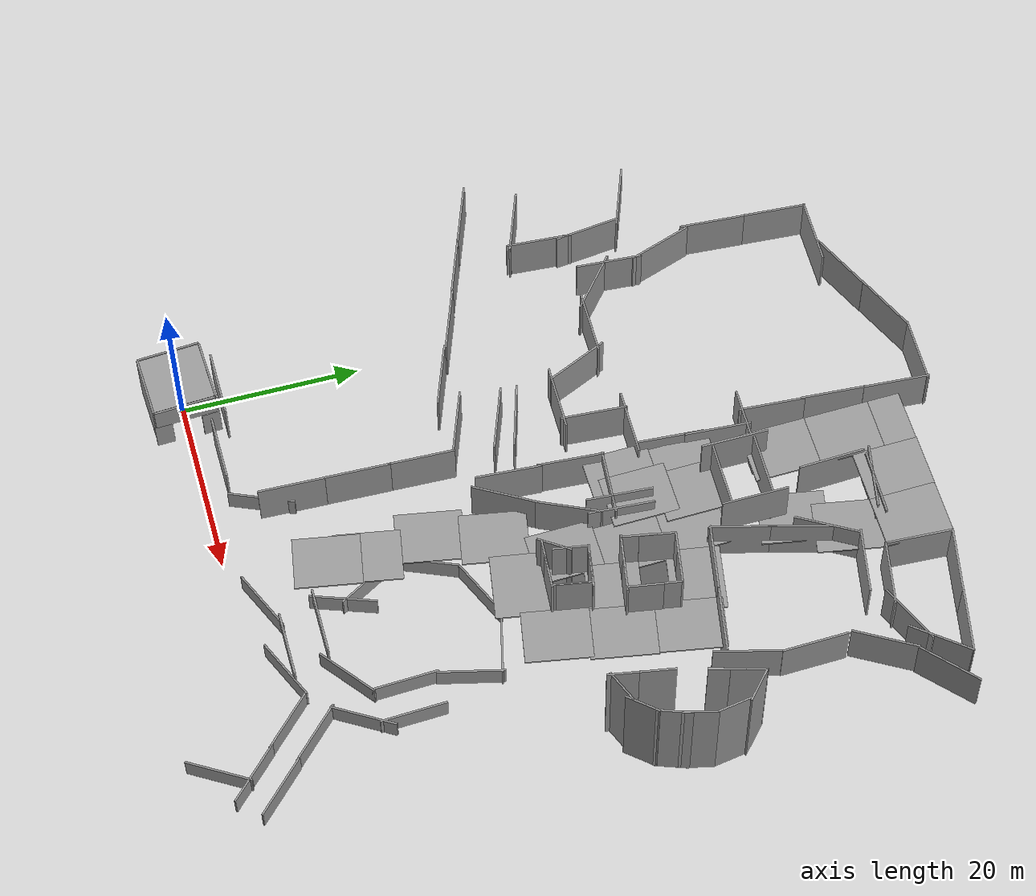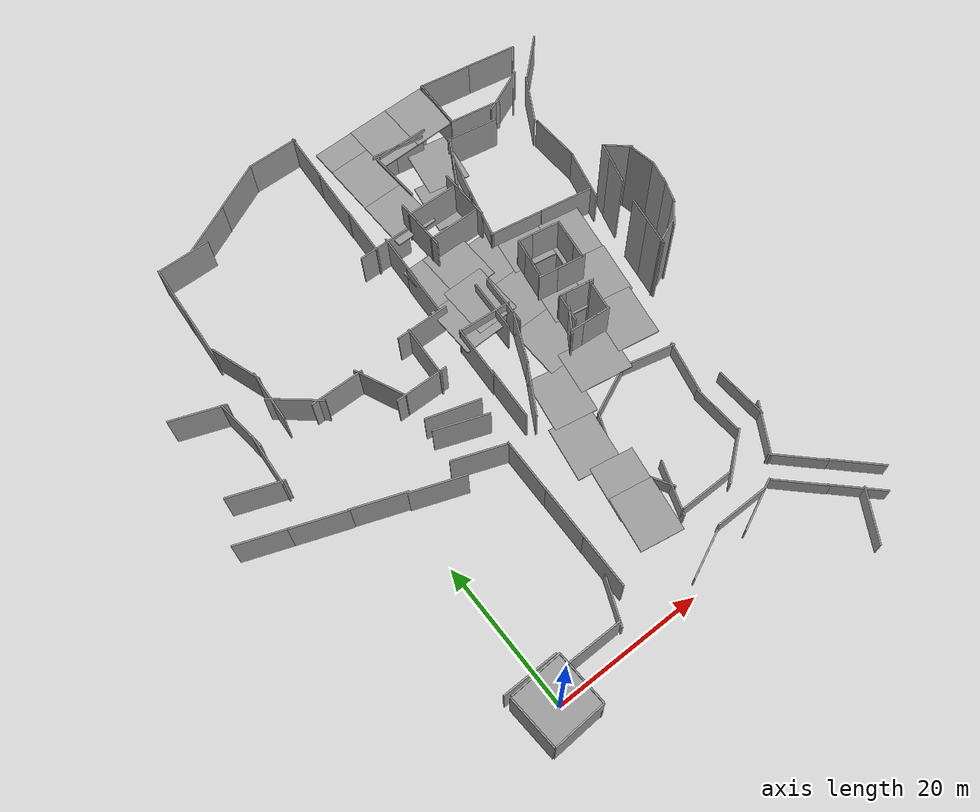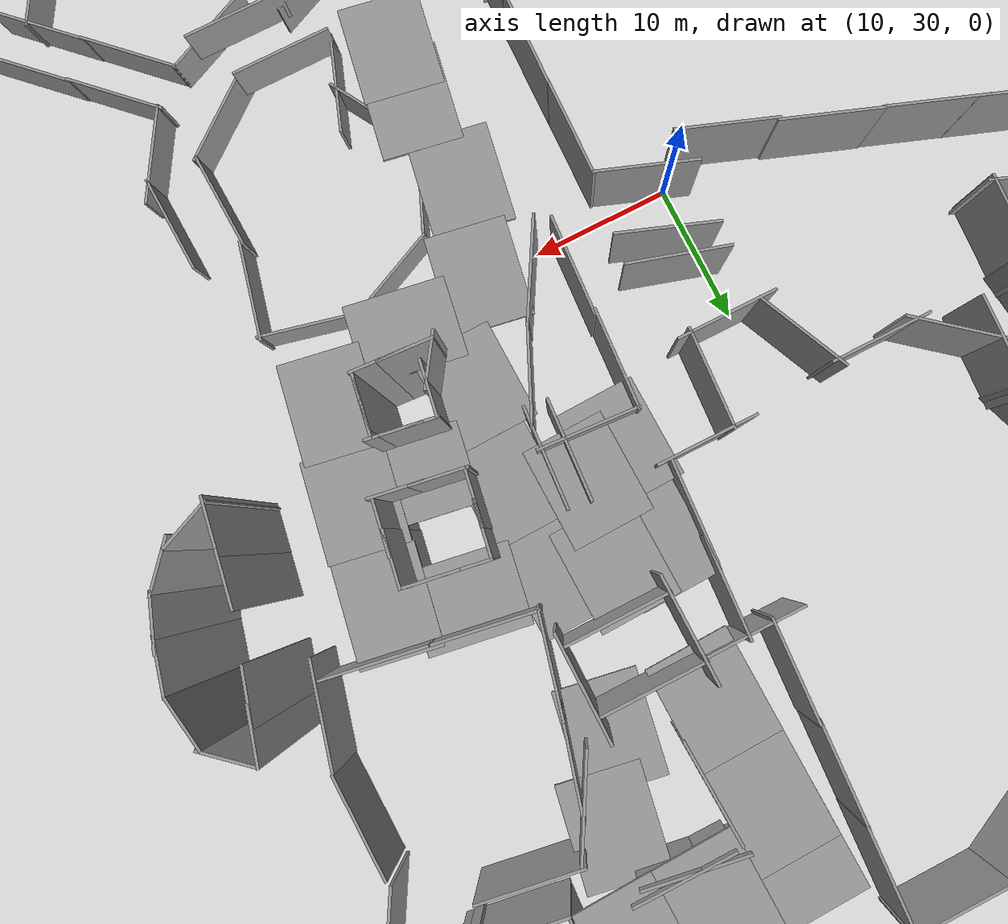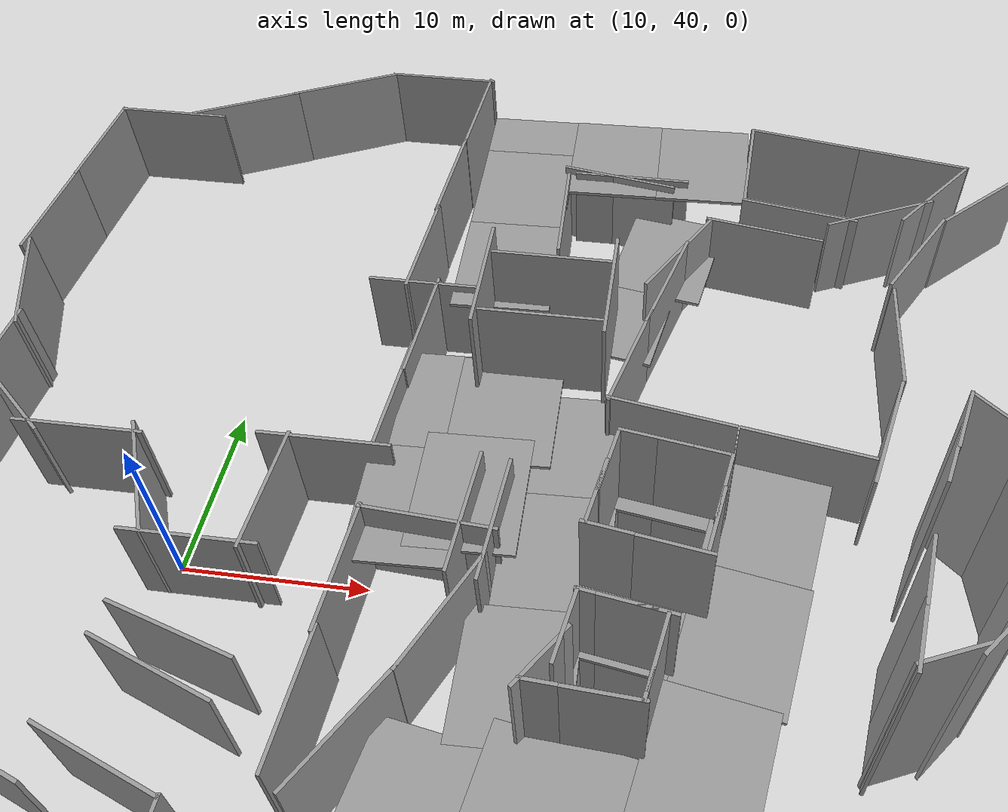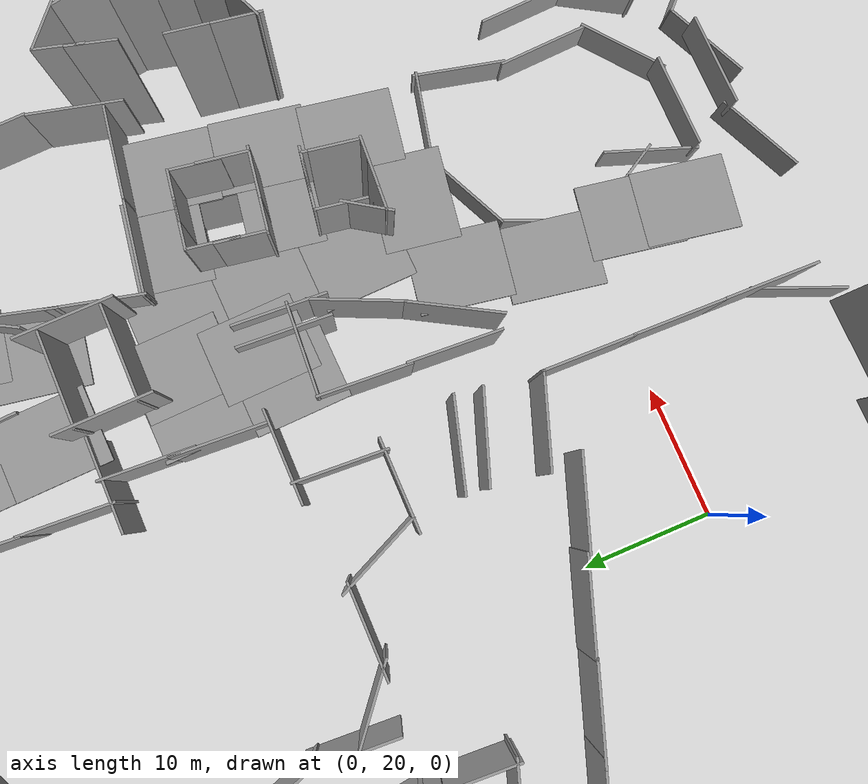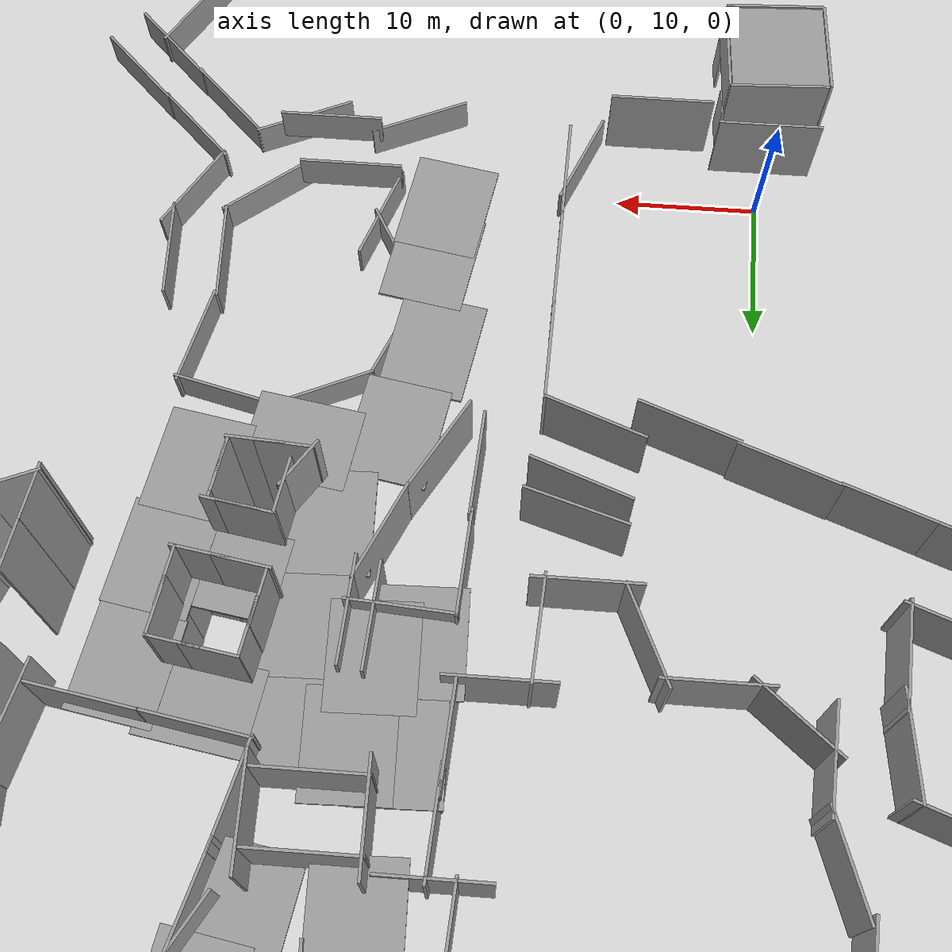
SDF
<sdf version="1.7">
 <world name="default">
  <light name="sun" type="directional">
   <pose>0 0 10 0 -0 0</pose>
   <diffuse>0.8 0.8 0.8 1</diffuse>
   <specular>0.2 0.2 0.2 1</specular>
   <attenuation>
    <range>1000</range>
    <constant>0.9</constant>
    <linear>0.01</linear>
    <quadratic>0.001</quadratic>
   </attenuation>
   <direction>-0.5 0.1 -0.9</direction>
   <spot><inner_angle>0</inner_angle><outer_angle>0</outer_angle><falloff>0</falloff></spot>
  </light>
  <gravity>0 0 -9.8</gravity>
  <magnetic_field>6e-06 2.3e-05 -4.2e-05</magnetic_field>
  <atmosphere type="adiabatic"/>
  <physics type="ode">
   <max_step_size>0.004</max_step_size>
   <real_time_factor>2</real_time_factor>
   <real_time_update_rate>1000</real_time_update_rate>
  </physics>
  <scene><ambient>0.4 0.4 0.4 1</ambient><background>0.7 0.7 0.7 1</background><shadows>1</shadows></scene>
  <spherical_coordinates>
   <surface_model>EARTH_WGS84</surface_model>
   <latitude_deg>0</latitude_deg>
   <longitude_deg>0</longitude_deg>
   <elevation>0</elevation>
   <heading_deg>0</heading_deg>
  </spherical_coordinates>
  <model name="grey_wall">
   <static>1</static>
   <link name="link">
    <pose>0 0 0 0 -0 1.57</pose>
    <collision name="collision"><geometry><box><size>7 0.2 7</size></box></geometry></collision>
    <visual name="visual">
     <cast_shadows>0</cast_shadows>
     <geometry><box><size>7 0.2 7</size></box></geometry>
     <material>
      <script>
       <uri>model://grey_wall/materials/scripts</uri>
       <uri>model://grey_wall/materials/textures</uri>
       <name>vrc/grey_wall</name>
      </script>
     </material>
    </visual>
   </link>
   <pose>-4.21474 -0.21131 2.80388 0 -0 0.06614</pose>
  </model>
  <model name="grey_wall_clone">
   <static>1</static>
   <link name="link">
    <pose>0 0 0 0 -0 1.57</pose>
    <collision name="collision"><geometry><box><size>7 0.2 7</size></box></geometry></collision>
    <visual name="visual">
     <cast_shadows>0</cast_shadows>
     <geometry><box><size>7 0.2 7</size></box></geometry>
     <material>
      <script>
       <uri>model://grey_wall/materials/scripts</uri>
       <uri>model://grey_wall/materials/textures</uri>
       <name>vrc/grey_wall</name>
      </script>
     </material>
    </visual>
   </link>
   <pose>-0.45009 -3.58157 2.80388 0 -0 1.62041</pose>
  </model>
  <model name="grey_wall_clone_clone">
   <static>1</static>
   <link name="link">
    <pose>0 0 0 0 -0 1.57</pose>
    <collision name="collision"><geometry><box><size>7 0.2 7</size></box></geometry></collision>
    <visual name="visual">
     <cast_shadows>0</cast_shadows>
     <geometry><box><size>7 0.2 7</size></box></geometry>
     <material>
      <script>
       <uri>model://grey_wall/materials/scripts</uri>
       <uri>model://grey_wall/materials/textures</uri>
       <name>vrc/grey_wall</name>
      </script>
     </material>
    </visual>
   </link>
   <pose>-0.789169 3.46124 2.80388 0 -0 1.62041</pose>
  </model>
  <model name="grey_wall_0">
   <static>1</static>
   <link name="link">
    <pose>0 0 0 0 -0 1.57</pose>
    <collision name="collision"><geometry><box><size>7 0.2 3</size></box></geometry></collision>
    <visual name="visual">
     <cast_shadows>0</cast_shadows>
     <geometry><box><size>7 0.2 3</size></box></geometry>
     <material>
      <script>
       <uri>model://grey_wall/materials/scripts</uri>
       <uri>model://grey_wall/materials/textures</uri>
       <name>vrc/grey_wall</name>
      </script>
     </material>
    </visual>
   </link>
   <pose>2.8837 0.111936 4.63934 0 -0 0.05281</pose>
  </model>
  <model name="grey_wall_1">
   <static>1</static>
   <link name="link">
    <pose>0 0 0 0 -0 1.57</pose>
    <collision name="collision"><geometry><box><size>2 0.2 4</size></box></geometry></collision>
    <visual name="visual">
     <cast_shadows>0</cast_shadows>
     <geometry><box><size>2 0.2 4</size></box></geometry>
     <material>
      <script>
       <uri>model://grey_wall/materials/scripts</uri>
       <uri>model://grey_wall/materials/textures</uri>
       <name>vrc/grey_wall</name>
      </script>
     </material>
    </visual>
   </link>
   <pose>2.92834 -2.58106 1.18435 0 -0 0.04294</pose>
  </model>
  <model name="grey_wall_1_clone">
   <static>1</static>
   <link name="link">
    <pose>0 0 0 0 -0 1.57</pose>
    <collision name="collision"><geometry><box><size>2 0.2 4</size></box></geometry></collision>
    <visual name="visual">
     <cast_shadows>0</cast_shadows>
     <geometry><box><size>2 0.2 4</size></box></geometry>
     <material>
      <script>
       <uri>model://grey_wall/materials/scripts</uri>
       <uri>model://grey_wall/materials/textures</uri>
       <name>vrc/grey_wall</name>
      </script>
     </material>
    </visual>
   </link>
   <pose>2.84535 2.76369 1.18435 0 -0 0.06626</pose>
  </model>
  <model name="grey_wall_2">
   <static>1</static>
   <link name="link">
    <pose>0 0 0 1.57 -0 1.57</pose>
    <collision name="collision"><geometry><box><size>7 0.2 7</size></box></geometry></collision>
    <visual name="visual">
     <cast_shadows>0</cast_shadows>
     <geometry><box><size>7 0.2 7</size></box></geometry>
     <material>
      <script>
       <uri>model://grey_wall/materials/scripts</uri>
       <uri>model://grey_wall/materials/textures</uri>
       <name>vrc/grey_wall</name>
      </script>
     </material>
    </visual>
   </link>
   <pose>-0.748455 -0.059649 6.04997 0 -0 0.0551</pose>
  </model>
  <model name="grey_wall_3">
   <static>1</static>
   <link name="link">
    <pose>0 0 1.4 0 -0 0</pose>
    <collision name="collision"><geometry><box><size>7.5 0.2 2.8</size></box></geometry></collision>
    <visual name="visual">
     <cast_shadows>0</cast_shadows>
     <geometry><box><size>7.5 0.2 2.8</size></box></geometry>
     <material>
      <script>
       <uri>model://grey_wall/materials/scripts</uri>
       <uri>model://grey_wall/materials/textures</uri>
       <name>vrc/grey_wall</name>
      </script>
     </material>
    </visual>
   </link>
   <pose>36.6898 26.9895 -3.10734 0 0 -0.23228</pose>
  </model>
  <model name="grey_wall_3_clone">
   <static>1</static>
   <link name="link">
    <pose>0 0 1.4 0 -0 0</pose>
    <collision name="collision"><geometry><box><size>7.5 0.2 2.8</size></box></geometry></collision>
    <visual name="visual">
     <cast_shadows>0</cast_shadows>
     <geometry><box><size>7.5 0.2 2.8</size></box></geometry>
     <material>
      <script>
       <uri>model://grey_wall/materials/scripts</uri>
       <uri>model://grey_wall/materials/textures</uri>
       <name>vrc/grey_wall</name>
      </script>
     </material>
    </visual>
   </link>
   <pose>29.6771 8.62683 -1.75695 0 -0 0</pose>
  </model>
  <model name="grey_wall_3_clone_0">
   <static>1</static>
   <link name="link">
    <pose>0 0 1.4 0 -0 0</pose>
    <collision name="collision"><geometry><box><size>7.5 0.2 2.8</size></box></geometry></collision>
    <visual name="visual">
     <cast_shadows>0</cast_shadows>
     <geometry><box><size>7.5 0.2 2.8</size></box></geometry>
     <material>
      <script>
       <uri>model://grey_wall/materials/scripts</uri>
       <uri>model://grey_wall/materials/textures</uri>
       <name>vrc/grey_wall</name>
      </script>
     </material>
    </visual>
   </link>
   <pose>29.8267 26.3383 -3.10734 0 -0 0.42913</pose>
  </model>
  <model name="grey_wall_3_clone_1">
   <static>1</static>
   <link name="link">
    <pose>0 0 1.4 0 -0 0</pose>
    <collision name="collision"><geometry><box><size>7.5 0.2 2.8</size></box></geometry></collision>
    <visual name="visual">
     <cast_shadows>0</cast_shadows>
     <geometry><box><size>7.5 0.2 2.8</size></box></geometry>
     <material>
      <script>
       <uri>model://grey_wall/materials/scripts</uri>
       <uri>model://grey_wall/materials/textures</uri>
       <name>vrc/grey_wall</name>
      </script>
     </material>
    </visual>
   </link>
   <pose>25.1126 21.4242 -3.10734 0 0 -1.9675</pose>
  </model>
  <model name="grey_wall_3_clone_2">
   <static>1</static>
   <link name="link">
    <pose>0 0 1.4 0 -0 0</pose>
    <collision name="collision"><geometry><box><size>7.5 0.2 2.8</size></box></geometry></collision>
    <visual name="visual">
     <cast_shadows>0</cast_shadows>
     <geometry><box><size>7.5 0.2 2.8</size></box></geometry>
     <material>
      <script>
       <uri>model://grey_wall/materials/scripts</uri>
       <uri>model://grey_wall/materials/textures</uri>
       <name>vrc/grey_wall</name>
      </script>
     </material>
    </visual>
   </link>
   <pose>25.7291 14.8094 -3.10734 0 0 -1.04617</pose>
  </model>
  <model name="grey_wall_3_clone_2_clone">
   <static>1</static>
   <link name="link">
    <pose>0 0 1.4 0 -0 0</pose>
    <collision name="collision"><geometry><box><size>7.5 0.2 2.8</size></box></geometry></collision>
    <visual name="visual">
     <cast_shadows>0</cast_shadows>
     <geometry><box><size>7.5 0.2 2.8</size></box></geometry>
     <material>
      <script>
       <uri>model://grey_wall/materials/scripts</uri>
       <uri>model://grey_wall/materials/textures</uri>
       <name>vrc/grey_wall</name>
      </script>
     </material>
    </visual>
   </link>
   <pose>38.4258 15.8633 -3.10734 0 0 -1.5271</pose>
  </model>
  <model name="grey_wall_3_clone_2_clone_0">
   <static>1</static>
   <link name="link">
    <pose>0 0 1.4 0 -0 0</pose>
    <collision name="collision"><geometry><box><size>7.5 0.2 2.8</size></box></geometry></collision>
    <visual name="visual">
     <cast_shadows>0</cast_shadows>
     <geometry><box><size>7.5 0.2 2.8</size></box></geometry>
     <material>
      <script>
       <uri>model://grey_wall/materials/scripts</uri>
       <uri>model://grey_wall/materials/textures</uri>
       <name>vrc/grey_wall</name>
      </script>
     </material>
    </visual>
   </link>
   <pose>39.2763 22.8874 -3.10734 0 0 -1.80366</pose>
  </model>
  <model name="grey_wall_3_clone_2_clone_1">
   <static>1</static>
   <link name="link">
    <pose>0 0 1.4 0 -0 0</pose>
    <collision name="collision"><geometry><box><size>7.5 0.2 2.8</size></box></geometry></collision>
    <visual name="visual">
     <cast_shadows>0</cast_shadows>
     <geometry><box><size>7.5 0.2 2.8</size></box></geometry>
     <material>
      <script>
       <uri>model://grey_wall/materials/scripts</uri>
       <uri>model://grey_wall/materials/textures</uri>
       <name>vrc/grey_wall</name>
      </script>
     </material>
    </visual>
   </link>
   <pose>27.193 11.7026 -3.10734 0 0 -1.91355</pose>
  </model>
  <model name="grey_wall_3_clone_2_clone_2">
   <static>1</static>
   <link name="link">
    <pose>0 0 1.4 0 -0 0</pose>
    <collision name="collision"><geometry><box><size>7.5 0.2 2.8</size></box></geometry></collision>
    <visual name="visual">
     <cast_shadows>0</cast_shadows>
     <geometry><box><size>7.5 0.2 2.8</size></box></geometry>
     <material>
      <script>
       <uri>model://grey_wall/materials/scripts</uri>
       <uri>model://grey_wall/materials/textures</uri>
       <name>vrc/grey_wall</name>
      </script>
     </material>
    </visual>
   </link>
   <pose>35.906 10.0574 -3.10734 0 0 -2.47034</pose>
  </model>
  <model name="grey_wall_4">
   <static>1</static>
   <link name="link">
    <pose>0 0 1.4 0 -0 0</pose>
    <collision name="collision"><geometry><box><size>7.5 0.2 6</size></box></geometry></collision>
    <visual name="visual">
     <cast_shadows>0</cast_shadows>
     <geometry><box><size>7.5 0.2 6</size></box></geometry>
     <material>
      <script>
       <uri>model://grey_wall/materials/scripts</uri>
       <uri>model://grey_wall/materials/textures</uri>
       <name>vrc/grey_wall</name>
      </script>
     </material>
    </visual>
   </link>
   <pose>16.0009 47.1151 -1.36031 0 -0 0</pose>
  </model>
  <model name="grey_wall_4_clone">
   <static>1</static>
   <link name="link">
    <pose>0 0 1.4 0 -0 0</pose>
    <collision name="collision"><geometry><box><size>7.5 0.2 6</size></box></geometry></collision>
    <visual name="visual">
     <cast_shadows>0</cast_shadows>
     <geometry><box><size>7.5 0.2 6</size></box></geometry>
     <material>
      <script>
       <uri>model://grey_wall/materials/scripts</uri>
       <uri>model://grey_wall/materials/textures</uri>
       <name>vrc/grey_wall</name>
      </script>
     </material>
    </visual>
   </link>
   <pose>19.1102 59.5367 -1.36031 0 -0 0</pose>
  </model>
  <model name="grey_wall_4_clone_0">
   <static>1</static>
   <link name="link">
    <pose>0 0 1.4 0 -0 0</pose>
    <collision name="collision"><geometry><box><size>7.5 0.2 6</size></box></geometry></collision>
    <visual name="visual">
     <cast_shadows>0</cast_shadows>
     <geometry><box><size>7.5 0.2 6</size></box></geometry>
     <material>
      <script>
       <uri>model://grey_wall/materials/scripts</uri>
       <uri>model://grey_wall/materials/textures</uri>
       <name>vrc/grey_wall</name>
      </script>
     </material>
    </visual>
   </link>
   <pose>10.8677 40.2516 -1.36031 0 -0 0</pose>
  </model>
  <model name="grey_wall_4_clone_1">
   <static>1</static>
   <link name="link">
    <pose>0 0 1.4 0 -0 0</pose>
    <collision name="collision"><geometry><box><size>7.5 0.2 6</size></box></geometry></collision>
    <visual name="visual">
     <cast_shadows>0</cast_shadows>
     <geometry><box><size>7.5 0.2 6</size></box></geometry>
     <material>
      <script>
       <uri>model://grey_wall/materials/scripts</uri>
       <uri>model://grey_wall/materials/textures</uri>
       <name>vrc/grey_wall</name>
      </script>
     </material>
    </visual>
   </link>
   <pose>2.43285 46.2968 -1.36031 0 -0 0</pose>
  </model>
  <model name="grey_wall_4_clone_2">
   <static>1</static>
   <link name="link">
    <pose>0 0 1.4 0 -0 0</pose>
    <collision name="collision"><geometry><box><size>7.5 0.2 6</size></box></geometry></collision>
    <visual name="visual">
     <cast_shadows>0</cast_shadows>
     <geometry><box><size>7.5 0.2 6</size></box></geometry>
     <material>
      <script>
       <uri>model://grey_wall/materials/scripts</uri>
       <uri>model://grey_wall/materials/textures</uri>
       <name>vrc/grey_wall</name>
      </script>
     </material>
    </visual>
   </link>
   <pose>15.4871 80.6091 -1.36031 0 -0 0</pose>
  </model>
  <model name="grey_wall_4_clone_3">
   <static>1</static>
   <link name="link">
    <pose>0 0 1.4 0 -0 0</pose>
    <collision name="collision"><geometry><box><size>7.5 0.2 6</size></box></geometry></collision>
    <visual name="visual">
     <cast_shadows>0</cast_shadows>
     <geometry><box><size>7.5 0.2 6</size></box></geometry>
     <material>
      <script>
       <uri>model://grey_wall/materials/scripts</uri>
       <uri>model://grey_wall/materials/textures</uri>
       <name>vrc/grey_wall</name>
      </script>
     </material>
    </visual>
   </link>
   <pose>8.62408 78.9708 -1.36031 0 -0 0.453296</pose>
  </model>
  <model name="grey_wall_4_clone_4">
   <static>1</static>
   <link name="link">
    <pose>0 0 1.4 0 -0 0</pose>
    <collision name="collision"><geometry><box><size>7.5 0.2 6</size></box></geometry></collision>
    <visual name="visual">
     <cast_shadows>0</cast_shadows>
     <geometry><box><size>7.5 0.2 6</size></box></geometry>
     <material>
      <script>
       <uri>model://grey_wall/materials/scripts</uri>
       <uri>model://grey_wall/materials/textures</uri>
       <name>vrc/grey_wall</name>
      </script>
     </material>
    </visual>
   </link>
   <pose>-2.54891 74.0503 -1.36031 0 -0 0</pose>
  </model>
  <model name="grey_wall_4_clone_5">
   <static>1</static>
   <link name="link">
    <pose>0 0 1.4 0 -0 0</pose>
    <collision name="collision"><geometry><box><size>7.5 0.2 6</size></box></geometry></collision>
    <visual name="visual">
     <cast_shadows>0</cast_shadows>
     <geometry><box><size>7.5 0.2 6</size></box></geometry>
     <material>
      <script>
       <uri>model://grey_wall/materials/scripts</uri>
       <uri>model://grey_wall/materials/textures</uri>
       <name>vrc/grey_wall</name>
      </script>
     </material>
    </visual>
   </link>
   <pose>18.7594 77.124 -1.36031 0 0 -1.63235</pose>
  </model>
  <model name="grey_wall_4_clone_5_clone">
   <static>1</static>
   <link name="link">
    <pose>0 0 1.4 0 -0 0</pose>
    <collision name="collision"><geometry><box><size>7.5 0.2 6</size></box></geometry></collision>
    <visual name="visual">
     <cast_shadows>0</cast_shadows>
     <geometry><box><size>7.5 0.2 6</size></box></geometry>
     <material>
      <script>
       <uri>model://grey_wall/materials/scripts</uri>
       <uri>model://grey_wall/materials/textures</uri>
       <name>vrc/grey_wall</name>
      </script>
     </material>
    </visual>
   </link>
   <pose>18.2913 69.9734 -1.36031 0 0 -1.63235</pose>
  </model>
  <model name="grey_wall_4_clone_5_clone_0">
   <static>1</static>
   <link name="link">
    <pose>0 0 1.4 0 -0 0</pose>
    <collision name="collision"><geometry><box><size>7.5 0.2 6</size></box></geometry></collision>
    <visual name="visual">
     <cast_shadows>0</cast_shadows>
     <geometry><box><size>7.5 0.2 6</size></box></geometry>
     <material>
      <script>
       <uri>model://grey_wall/materials/scripts</uri>
       <uri>model://grey_wall/materials/textures</uri>
       <name>vrc/grey_wall</name>
      </script>
     </material>
    </visual>
   </link>
   <pose>17.9317 62.9217 -1.36031 0 0 -1.63235</pose>
  </model>
  <model name="grey_wall_4_clone_5_clone_1">
   <static>1</static>
   <link name="link">
    <pose>0 0 1.4 0 -0 0</pose>
    <collision name="collision"><geometry><box><size>7.5 0.2 6</size></box></geometry></collision>
    <visual name="visual">
     <cast_shadows>0</cast_shadows>
     <geometry><box><size>7.5 0.2 6</size></box></geometry>
     <material>
      <script>
       <uri>model://grey_wall/materials/scripts</uri>
       <uri>model://grey_wall/materials/textures</uri>
       <name>vrc/grey_wall</name>
      </script>
     </material>
    </visual>
   </link>
   <pose>18.9558 50.955 -1.36031 0 0 -1.63235</pose>
  </model>
  <model name="grey_wall_4_clone_5_clone_2">
   <static>1</static>
   <link name="link">
    <pose>0 0 1.4 0 -0 0</pose>
    <collision name="collision"><geometry><box><size>7.5 0.2 6</size></box></geometry></collision>
    <visual name="visual">
     <cast_shadows>0</cast_shadows>
     <geometry><box><size>7.5 0.2 6</size></box></geometry>
     <material>
      <script>
       <uri>model://grey_wall/materials/scripts</uri>
       <uri>model://grey_wall/materials/textures</uri>
       <name>vrc/grey_wall</name>
      </script>
     </material>
    </visual>
   </link>
   <pose>19.3647 56.2613 -1.36031 0 0 -1.63235</pose>
  </model>
  <model name="grey_wall_4_clone_5_clone_3">
   <static>1</static>
   <link name="link">
    <pose>0 0 1.4 0 -0 0</pose>
    <collision name="collision"><geometry><box><size>7.5 0.2 6</size></box></geometry></collision>
    <visual name="visual">
     <cast_shadows>0</cast_shadows>
     <geometry><box><size>7.5 0.2 6</size></box></geometry>
     <material>
      <script>
       <uri>model://grey_wall/materials/scripts</uri>
       <uri>model://grey_wall/materials/textures</uri>
       <name>vrc/grey_wall</name>
      </script>
     </material>
    </visual>
   </link>
   <pose>13.8066 43.613 -1.36031 0 0 -1.63235</pose>
  </model>
  <model name="grey_wall_4_clone_5_clone_4">
   <static>1</static>
   <link name="link">
    <pose>0 0 1.4 0 -0 0</pose>
    <collision name="collision"><geometry><box><size>7.5 0.2 6</size></box></geometry></collision>
    <visual name="visual">
     <cast_shadows>0</cast_shadows>
     <geometry><box><size>7.5 0.2 6</size></box></geometry>
     <material>
      <script>
       <uri>model://grey_wall/materials/scripts</uri>
       <uri>model://grey_wall/materials/textures</uri>
       <name>vrc/grey_wall</name>
      </script>
     </material>
    </visual>
   </link>
   <pose>6.91976 43.5617 -1.36031 0 0 -1.15044</pose>
  </model>
  <model name="grey_wall_4_clone_5_clone_5">
   <static>1</static>
   <link name="link">
    <pose>0 0 1.4 0 -0 0</pose>
    <collision name="collision"><geometry><box><size>7.5 0.2 6</size></box></geometry></collision>
    <visual name="visual">
     <cast_shadows>0</cast_shadows>
     <geometry><box><size>7.5 0.2 6</size></box></geometry>
     <material>
      <script>
       <uri>model://grey_wall/materials/scripts</uri>
       <uri>model://grey_wall/materials/textures</uri>
       <name>vrc/grey_wall</name>
      </script>
     </material>
    </visual>
   </link>
   <pose>-6.39185 70.4672 -1.36031 0 0 -1.63235</pose>
  </model>
  <model name="grey_wall_4_clone_5_clone_6">
   <static>1</static>
   <link name="link">
    <pose>0 0 1.4 0 -0 0</pose>
    <collision name="collision"><geometry><box><size>7.5 0.2 6</size></box></geometry></collision>
    <visual name="visual">
     <cast_shadows>0</cast_shadows>
     <geometry><box><size>7.5 0.2 6</size></box></geometry>
     <material>
      <script>
       <uri>model://grey_wall/materials/scripts</uri>
       <uri>model://grey_wall/materials/textures</uri>
       <name>vrc/grey_wall</name>
      </script>
     </material>
    </visual>
   </link>
   <pose>-6.80635 63.2942 -1.36031 0 0 -1.63235</pose>
  </model>
  <model name="grey_wall_4_clone_5_clone_7">
   <static>1</static>
   <link name="link">
    <pose>0 0 1.4 0 -0 0</pose>
    <collision name="collision"><geometry><box><size>7.5 0.2 6</size></box></geometry></collision>
    <visual name="visual">
     <cast_shadows>0</cast_shadows>
     <geometry><box><size>7.5 0.2 6</size></box></geometry>
     <material>
      <script>
       <uri>model://grey_wall/materials/scripts</uri>
       <uri>model://grey_wall/materials/textures</uri>
       <name>vrc/grey_wall</name>
      </script>
     </material>
    </visual>
   </link>
   <pose>-5.58672 56.7985 -1.36031 0 0 -1.24275</pose>
  </model>
  <model name="grey_wall_4_clone_5_clone_8">
   <static>1</static>
   <link name="link">
    <pose>0 0 1.4 0 -0 0</pose>
    <collision name="collision"><geometry><box><size>7.5 0.2 6</size></box></geometry></collision>
    <visual name="visual">
     <cast_shadows>0</cast_shadows>
     <geometry><box><size>7.5 0.2 6</size></box></geometry>
     <material>
      <script>
       <uri>model://grey_wall/materials/scripts</uri>
       <uri>model://grey_wall/materials/textures</uri>
       <name>vrc/grey_wall</name>
      </script>
     </material>
    </visual>
   </link>
   <pose>-4.72145 50.5528 -1.36031 0 0 -1.63235</pose>
  </model>
  <model name="grey_wall_4_clone_5_clone_9">
   <static>1</static>
   <link name="link">
    <pose>0 0 1.4 0 -0 0</pose>
    <collision name="collision"><geometry><box><size>7.5 0.2 6</size></box></geometry></collision>
    <visual name="visual">
     <cast_shadows>0</cast_shadows>
     <geometry><box><size>7.5 0.2 6</size></box></geometry>
     <material>
      <script>
       <uri>model://grey_wall/materials/scripts</uri>
       <uri>model://grey_wall/materials/textures</uri>
       <name>vrc/grey_wall</name>
      </script>
     </material>
    </visual>
   </link>
   <pose>-2.54426 48.1501 -1.36031 0 0 -0.694859</pose>
  </model>
  <model name="grey_wall_4_clone_5_clone_10">
   <static>1</static>
   <link name="link">
    <pose>0 0 1.4 0 -0 0</pose>
    <collision name="collision"><geometry><box><size>7.5 0.2 6</size></box></geometry></collision>
    <visual name="visual">
     <cast_shadows>0</cast_shadows>
     <geometry><box><size>7.5 0.2 6</size></box></geometry>
     <material>
      <script>
       <uri>model://grey_wall/materials/scripts</uri>
       <uri>model://grey_wall/materials/textures</uri>
       <name>vrc/grey_wall</name>
      </script>
     </material>
    </visual>
   </link>
   <pose>26.0391 43.3199 -1.36031 0 0 -1.63235</pose>
  </model>
  <model name="grey_wall_4_clone_5_clone_11">
   <static>1</static>
   <link name="link">
    <pose>0 0 1.4 0 -0 0</pose>
    <collision name="collision"><geometry><box><size>7.5 0.2 6</size></box></geometry></collision>
    <visual name="visual">
     <cast_shadows>0</cast_shadows>
     <geometry><box><size>7.5 0.2 6</size></box></geometry>
     <material>
      <script>
       <uri>model://grey_wall/materials/scripts</uri>
       <uri>model://grey_wall/materials/textures</uri>
       <name>vrc/grey_wall</name>
      </script>
     </material>
    </visual>
   </link>
   <pose>24.4499 37.8323 -1.36031 0 0 -1.99581</pose>
  </model>
  <model name="grey_wall_4_clone_5_clone_12">
   <static>1</static>
   <link name="link">
    <pose>0 0 1.4 0 -0 0</pose>
    <collision name="collision"><geometry><box><size>7.5 0.2 6</size></box></geometry></collision>
    <visual name="visual">
     <cast_shadows>0</cast_shadows>
     <geometry><box><size>7.5 0.2 6</size></box></geometry>
     <material>
      <script>
       <uri>model://grey_wall/materials/scripts</uri>
       <uri>model://grey_wall/materials/textures</uri>
       <name>vrc/grey_wall</name>
      </script>
     </material>
    </visual>
   </link>
   <pose>21.1469 31.4317 -1.36031 0 0 -2.09189</pose>
  </model>
  <model name="grey_wall_4_clone_5_clone_13">
   <static>1</static>
   <link name="link">
    <pose>0 0 1.4 0 -0 0</pose>
    <collision name="collision"><geometry><box><size>7.5 0.2 6</size></box></geometry></collision>
    <visual name="visual">
     <cast_shadows>0</cast_shadows>
     <geometry><box><size>7.5 0.2 6</size></box></geometry>
     <material>
      <script>
       <uri>model://grey_wall/materials/scripts</uri>
       <uri>model://grey_wall/materials/textures</uri>
       <name>vrc/grey_wall</name>
      </script>
     </material>
    </visual>
   </link>
   <pose>18.8306 39.5838 -1.36031 0 0 -1.63235</pose>
  </model>
  <model name="grey_wall_4_clone_5_clone_14">
   <static>1</static>
   <link name="link">
    <pose>0 0 1.4 0 -0 0</pose>
    <collision name="collision"><geometry><box><size>7.5 0.2 6</size></box></geometry></collision>
    <visual name="visual">
     <cast_shadows>0</cast_shadows>
     <geometry><box><size>7.5 0.2 6</size></box></geometry>
     <material>
      <script>
       <uri>model://grey_wall/materials/scripts</uri>
       <uri>model://grey_wall/materials/textures</uri>
       <name>vrc/grey_wall</name>
      </script>
     </material>
    </visual>
   </link>
   <pose>18.5329 32.5931 -1.36031 0 0 -1.63235</pose>
  </model>
  <model name="grey_wall_4_clone_5_clone_15">
   <static>1</static>
   <link name="link">
    <pose>0 0 1.4 0 -0 0</pose>
    <collision name="collision"><geometry><box><size>7.5 0.2 6</size></box></geometry></collision>
    <visual name="visual">
     <cast_shadows>0</cast_shadows>
     <geometry><box><size>7.5 0.2 6</size></box></geometry>
     <material>
      <script>
       <uri>model://grey_wall/materials/scripts</uri>
       <uri>model://grey_wall/materials/textures</uri>
       <name>vrc/grey_wall</name>
      </script>
     </material>
    </visual>
   </link>
   <pose>24.4072 43.5806 -1.36031 0 0 -1.63235</pose>
  </model>
  <model name="grey_wall_4_clone_5_clone_16">
   <static>1</static>
   <link name="link">
    <pose>0 0 1.4 0 -0 0</pose>
    <collision name="collision"><geometry><box><size>7.5 0.2 6</size></box></geometry></collision>
    <visual name="visual">
     <cast_shadows>0</cast_shadows>
     <geometry><box><size>7.5 0.2 6</size></box></geometry>
     <material>
      <script>
       <uri>model://grey_wall/materials/scripts</uri>
       <uri>model://grey_wall/materials/textures</uri>
       <name>vrc/grey_wall</name>
      </script>
     </material>
    </visual>
   </link>
   <pose>22.6409 42.8769 -1.36031 0 0 -0.067363</pose>
  </model>
  <model name="grey_wall_4_clone_0_clone">
   <static>1</static>
   <link name="link">
    <pose>0 0 1.4 0 -0 0</pose>
    <collision name="collision"><geometry><box><size>7.5 0.2 6</size></box></geometry></collision>
    <visual name="visual">
     <cast_shadows>0</cast_shadows>
     <geometry><box><size>7.5 0.2 6</size></box></geometry>
     <material>
      <script>
       <uri>model://grey_wall/materials/scripts</uri>
       <uri>model://grey_wall/materials/textures</uri>
       <name>vrc/grey_wall</name>
      </script>
     </material>
    </visual>
   </link>
   <pose>11.8576 35.1709 -1.36031 0 0 -0.293082</pose>
  </model>
  <model name="grey_wall_4_clone_0_clone_0">
   <static>1</static>
   <link name="link">
    <pose>0 0 1.4 0 -0 0</pose>
    <collision name="collision"><geometry><box><size>7.5 0.2 6</size></box></geometry></collision>
    <visual name="visual">
     <cast_shadows>0</cast_shadows>
     <geometry><box><size>7.5 0.2 6</size></box></geometry>
     <material>
      <script>
       <uri>model://grey_wall/materials/scripts</uri>
       <uri>model://grey_wall/materials/textures</uri>
       <name>vrc/grey_wall</name>
      </script>
     </material>
    </visual>
   </link>
   <pose>11.6182 33.1775 -1.36031 0 0 -0.351253</pose>
  </model>
  <model name="grey_wall_4_clone_0_clone_1">
   <static>1</static>
   <link name="link">
    <pose>0 0 1.4 0 -0 0</pose>
    <collision name="collision"><geometry><box><size>7.5 0.2 6</size></box></geometry></collision>
    <visual name="visual">
     <cast_shadows>0</cast_shadows>
     <geometry><box><size>7.5 0.2 6</size></box></geometry>
     <material>
      <script>
       <uri>model://grey_wall/materials/scripts</uri>
       <uri>model://grey_wall/materials/textures</uri>
       <name>vrc/grey_wall</name>
      </script>
     </material>
    </visual>
   </link>
   <pose>14.2703 23.8615 -1.36031 0 0 -1.59956</pose>
  </model>
  <model name="grey_wall_4_clone_0_clone_1_clone">
   <static>1</static>
   <link name="link">
    <pose>0 0 1.4 0 -0 0</pose>
    <collision name="collision"><geometry><box><size>7.5 0.2 6</size></box></geometry></collision>
    <visual name="visual">
     <cast_shadows>0</cast_shadows>
     <geometry><box><size>7.5 0.2 6</size></box></geometry>
     <material>
      <script>
       <uri>model://grey_wall/materials/scripts</uri>
       <uri>model://grey_wall/materials/textures</uri>
       <name>vrc/grey_wall</name>
      </script>
     </material>
    </visual>
   </link>
   <pose>14.0835 16.6333 -1.36031 0 0 -1.59956</pose>
  </model>
  <model name="grey_wall_4_clone_0_clone_1_clone_0">
   <static>1</static>
   <link name="link">
    <pose>0 0 1.4 0 -0 0</pose>
    <collision name="collision"><geometry><box><size>7.5 0.2 6</size></box></geometry></collision>
    <visual name="visual">
     <cast_shadows>0</cast_shadows>
     <geometry><box><size>7.5 0.2 6</size></box></geometry>
     <material>
      <script>
       <uri>model://grey_wall/materials/scripts</uri>
       <uri>model://grey_wall/materials/textures</uri>
       <name>vrc/grey_wall</name>
      </script>
     </material>
    </visual>
   </link>
   <pose>13.889 9.28364 -1.36031 0 0 -1.59956</pose>
  </model>
  <model name="grey_wall_4_clone_0_clone_0_clone">
   <static>1</static>
   <link name="link">
    <pose>0 0 1.4 0 -0 0</pose>
    <collision name="collision"><geometry><box><size>7.5 0.2 6</size></box></geometry></collision>
    <visual name="visual">
     <cast_shadows>0</cast_shadows>
     <geometry><box><size>7.5 0.2 6</size></box></geometry>
     <material>
      <script>
       <uri>model://grey_wall/materials/scripts</uri>
       <uri>model://grey_wall/materials/textures</uri>
       <name>vrc/grey_wall</name>
      </script>
     </material>
    </visual>
   </link>
   <pose>10.9004 28.6993 -1.36031 0 0 -0.351253</pose>
  </model>
  <model name="grey_wall_4_clone_0_clone_0_clone_0">
   <static>1</static>
   <link name="link">
    <pose>0 0 1.4 0 -0 0</pose>
    <collision name="collision"><geometry><box><size>7.5 0.2 6</size></box></geometry></collision>
    <visual name="visual">
     <cast_shadows>0</cast_shadows>
     <geometry><box><size>7.5 0.2 6</size></box></geometry>
     <material>
      <script>
       <uri>model://grey_wall/materials/scripts</uri>
       <uri>model://grey_wall/materials/textures</uri>
       <name>vrc/grey_wall</name>
      </script>
     </material>
    </visual>
   </link>
   <pose>4.61691 28.5572 -1.36031 0 0 -0.351253</pose>
  </model>
  <model name="grey_wall_4_clone_0_clone_0_clone_1">
   <static>1</static>
   <link name="link">
    <pose>0 0 1.4 0 -0 0</pose>
    <collision name="collision"><geometry><box><size>7.5 0.2 6</size></box></geometry></collision>
    <visual name="visual">
     <cast_shadows>0</cast_shadows>
     <geometry><box><size>7.5 0.2 6</size></box></geometry>
     <material>
      <script>
       <uri>model://grey_wall/materials/scripts</uri>
       <uri>model://grey_wall/materials/textures</uri>
       <name>vrc/grey_wall</name>
      </script>
     </material>
    </visual>
   </link>
   <pose>-2.08883 31.1935 -1.36031 0 0 -0.351253</pose>
  </model>
  <model name="grey_wall_4_clone_0_clone_0_clone_2">
   <static>1</static>
   <link name="link">
    <pose>0 0 1.4 0 -0 0</pose>
    <collision name="collision"><geometry><box><size>7.5 0.2 6</size></box></geometry></collision>
    <visual name="visual">
     <cast_shadows>0</cast_shadows>
     <geometry><box><size>7.5 0.2 6</size></box></geometry>
     <material>
      <script>
       <uri>model://grey_wall/materials/scripts</uri>
       <uri>model://grey_wall/materials/textures</uri>
       <name>vrc/grey_wall</name>
      </script>
     </material>
    </visual>
   </link>
   <pose>-8.90977 33.6237 -1.36031 0 0 -0.351253</pose>
  </model>
  <model name="grey_wall_4_clone_0_clone_0_clone_3">
   <static>1</static>
   <link name="link">
    <pose>0 0 1.4 0 -0 0</pose>
    <collision name="collision"><geometry><box><size>7.5 0.2 6</size></box></geometry></collision>
    <visual name="visual">
     <cast_shadows>0</cast_shadows>
     <geometry><box><size>7.5 0.2 6</size></box></geometry>
     <material>
      <script>
       <uri>model://grey_wall/materials/scripts</uri>
       <uri>model://grey_wall/materials/textures</uri>
       <name>vrc/grey_wall</name>
      </script>
     </material>
    </visual>
   </link>
   <pose>-15.1705 35.9303 -1.36031 0 0 -0.351253</pose>
  </model>
  <model name="grey_wall_4_clone_0_clone_0_clone_4">
   <static>1</static>
   <link name="link">
    <pose>0 0 1.4 0 -0 0</pose>
    <collision name="collision"><geometry><box><size>7.5 0.2 6</size></box></geometry></collision>
    <visual name="visual">
     <cast_shadows>0</cast_shadows>
     <geometry><box><size>7.5 0.2 6</size></box></geometry>
     <material>
      <script>
       <uri>model://grey_wall/materials/scripts</uri>
       <uri>model://grey_wall/materials/textures</uri>
       <name>vrc/grey_wall</name>
      </script>
     </material>
    </visual>
   </link>
   <pose>-12.7232 41.42 -1.36031 0 0 -0.351253</pose>
  </model>
  <model name="grey_wall_4_clone_0_clone_0_clone_5">
   <static>1</static>
   <link name="link">
    <pose>0 0 1.4 0 -0 0</pose>
    <collision name="collision"><geometry><box><size>7.5 0.2 6</size></box></geometry></collision>
    <visual name="visual">
     <cast_shadows>0</cast_shadows>
     <geometry><box><size>7.5 0.2 6</size></box></geometry>
     <material>
      <script>
       <uri>model://grey_wall/materials/scripts</uri>
       <uri>model://grey_wall/materials/textures</uri>
       <name>vrc/grey_wall</name>
      </script>
     </material>
    </visual>
   </link>
   <pose>-12.8399 53.9974 -1.36031 0 0 -0.351253</pose>
  </model>
  <model name="grey_wall_4_clone_0_clone_0_clone_6">
   <static>1</static>
   <link name="link">
    <pose>0 0 1.4 0 -0 0</pose>
    <collision name="collision"><geometry><box><size>7.5 0.2 6</size></box></geometry></collision>
    <visual name="visual">
     <cast_shadows>0</cast_shadows>
     <geometry><box><size>7.5 0.2 6</size></box></geometry>
     <material>
      <script>
       <uri>model://grey_wall/materials/scripts</uri>
       <uri>model://grey_wall/materials/textures</uri>
       <name>vrc/grey_wall</name>
      </script>
     </material>
    </visual>
   </link>
   <pose>-0.78334 4.38162 -1.36031 0 -0 0.004291</pose>
  </model>
  <model name="grey_wall_4_clone_0_clone_1_clone_1">
   <static>1</static>
   <link name="link">
    <pose>0 0 1.4 0 -0 0</pose>
    <collision name="collision"><geometry><box><size>7.5 0.2 6</size></box></geometry></collision>
    <visual name="visual">
     <cast_shadows>0</cast_shadows>
     <geometry><box><size>7.5 0.2 6</size></box></geometry>
     <material>
      <script>
       <uri>model://grey_wall/materials/scripts</uri>
       <uri>model://grey_wall/materials/textures</uri>
       <name>vrc/grey_wall</name>
      </script>
     </material>
    </visual>
   </link>
   <pose>-9.56386 49.3439 -1.36031 0 0 -1.45172</pose>
  </model>
  <model name="grey_wall_4_clone_5_clone_3_clone">
   <static>1</static>
   <link name="link">
    <pose>0 0 1.4 0 -0 0</pose>
    <collision name="collision"><geometry><box><size>7.5 0.2 6</size></box></geometry></collision>
    <visual name="visual">
     <cast_shadows>0</cast_shadows>
     <geometry><box><size>7.5 0.2 6</size></box></geometry>
     <material>
      <script>
       <uri>model://grey_wall/materials/scripts</uri>
       <uri>model://grey_wall/materials/textures</uri>
       <name>vrc/grey_wall</name>
      </script>
     </material>
    </visual>
   </link>
   <pose>-9.49011 43.6181 -1.36031 0 0 -1.63235</pose>
  </model>
  <model name="grey_wall_4_clone_0_clone_0_clone_6_clone">
   <static>1</static>
   <link name="link">
    <pose>0 0 1.4 0 -0 0</pose>
    <collision name="collision"><geometry><box><size>7.5 0.2 6</size></box></geometry></collision>
    <visual name="visual">
     <cast_shadows>0</cast_shadows>
     <geometry><box><size>7.5 0.2 6</size></box></geometry>
     <material>
      <script>
       <uri>model://grey_wall/materials/scripts</uri>
       <uri>model://grey_wall/materials/textures</uri>
       <name>vrc/grey_wall</name>
      </script>
     </material>
    </visual>
   </link>
   <pose>7.1515 2.73217 -1.36031 0 -0 0.004291</pose>
  </model>
  <model name="grey_wall_3_clone_1_clone">
   <static>1</static>
   <link name="link">
    <pose>0 0 1.4 0 -0 0</pose>
    <collision name="collision"><geometry><box><size>7.5 0.2 2.8</size></box></geometry></collision>
    <visual name="visual">
     <cast_shadows>0</cast_shadows>
     <geometry><box><size>7.5 0.2 2.8</size></box></geometry>
     <material>
      <script>
       <uri>model://grey_wall/materials/scripts</uri>
       <uri>model://grey_wall/materials/textures</uri>
       <name>vrc/grey_wall</name>
      </script>
     </material>
    </visual>
   </link>
   <pose>12.7235 5.94853 -3.10734 0 0 -1.9675</pose>
  </model>
  <model name="grey_wall_4_clone_5_clone_0_clone">
   <static>1</static>
   <link name="link">
    <pose>0 0 1.4 0 -0 0</pose>
    <collision name="collision"><geometry><box><size>7.5 0.2 6</size></box></geometry></collision>
    <visual name="visual">
     <cast_shadows>0</cast_shadows>
     <geometry><box><size>7.5 0.2 6</size></box></geometry>
     <material>
      <script>
       <uri>model://grey_wall/materials/scripts</uri>
       <uri>model://grey_wall/materials/textures</uri>
       <name>vrc/grey_wall</name>
      </script>
     </material>
    </visual>
   </link>
   <pose>46.3083 51.5827 -1.36031 0 0 -1.81447</pose>
  </model>
  <model name="grey_wall_4_clone_5_clone_0_clone_clone">
   <static>1</static>
   <link name="link">
    <pose>0 0 1.4 0 -0 0</pose>
    <collision name="collision"><geometry><box><size>7.5 0.2 6</size></box></geometry></collision>
    <visual name="visual">
     <cast_shadows>0</cast_shadows>
     <geometry><box><size>7.5 0.2 6</size></box></geometry>
     <material>
      <script>
       <uri>model://grey_wall/materials/scripts</uri>
       <uri>model://grey_wall/materials/textures</uri>
       <name>vrc/grey_wall</name>
      </script>
     </material>
    </visual>
   </link>
   <pose>31.8033 55.374 -1.36031 0 0 -1.81447</pose>
  </model>
  <model name="grey_wall_4_clone_5_clone_0_clone_clone_0">
   <static>1</static>
   <link name="link">
    <pose>0 0 1.4 0 -0 0</pose>
    <collision name="collision"><geometry><box><size>7.5 0.2 6</size></box></geometry></collision>
    <visual name="visual">
     <cast_shadows>0</cast_shadows>
     <geometry><box><size>7.5 0.2 6</size></box></geometry>
     <material>
      <script>
       <uri>model://grey_wall/materials/scripts</uri>
       <uri>model://grey_wall/materials/textures</uri>
       <name>vrc/grey_wall</name>
      </script>
     </material>
    </visual>
   </link>
   <pose>33.4296 61.6318 -1.36031 0 0 -1.83467</pose>
  </model>
  <model name="grey_wall_4_clone_5_clone_0_clone_clone_2">
   <static>1</static>
   <link name="link">
    <pose>0 0 1.4 0 -0 0</pose>
    <collision name="collision"><geometry><box><size>7.5 0.2 6</size></box></geometry></collision>
    <visual name="visual">
     <cast_shadows>0</cast_shadows>
     <geometry><box><size>7.5 0.2 6</size></box></geometry>
     <material>
      <script>
       <uri>model://grey_wall/materials/scripts</uri>
       <uri>model://grey_wall/materials/textures</uri>
       <name>vrc/grey_wall</name>
      </script>
     </material>
    </visual>
   </link>
   <pose>48.7352 66.2029 -1.36031 0 0 -2.08831</pose>
  </model>
  <model name="grey_wall_4_clone_5_clone_0_clone_clone_0_clone">
   <static>1</static>
   <link name="link">
    <pose>0 0 1.4 0 -0 0</pose>
    <collision name="collision"><geometry><box><size>7.5 0.2 6</size></box></geometry></collision>
    <visual name="visual">
     <cast_shadows>0</cast_shadows>
     <geometry><box><size>7.5 0.2 6</size></box></geometry>
     <material>
      <script>
       <uri>model://grey_wall/materials/scripts</uri>
       <uri>model://grey_wall/materials/textures</uri>
       <name>vrc/grey_wall</name>
      </script>
     </material>
    </visual>
   </link>
   <pose>47.1665 58.9116 -1.36031 0 0 -1.54099</pose>
  </model>
  <model name="grey_wall_4_clone_5_clone_0_clone_clone_1_clone_0">
   <static>1</static>
   <link name="link">
    <pose>0 0 1.4 0 -0 0</pose>
    <collision name="collision"><geometry><box><size>7.5 0.2 6</size></box></geometry></collision>
    <visual name="visual">
     <cast_shadows>0</cast_shadows>
     <geometry><box><size>7.5 0.2 6</size></box></geometry>
     <material>
      <script>
       <uri>model://grey_wall/materials/scripts</uri>
       <uri>model://grey_wall/materials/textures</uri>
       <name>vrc/grey_wall</name>
      </script>
     </material>
    </visual>
   </link>
   <pose>34.4569 51.3738 -1.36031 0 -0 2.97634</pose>
  </model>
  <model name="grey_wall_4_clone_5_clone_0_clone_clone_1_clone_1">
   <static>1</static>
   <link name="link">
    <pose>0 0 1.4 0 -0 0</pose>
    <collision name="collision"><geometry><box><size>7.5 0.2 6</size></box></geometry></collision>
    <visual name="visual">
     <cast_shadows>0</cast_shadows>
     <geometry><box><size>7.5 0.2 6</size></box></geometry>
     <material>
      <script>
       <uri>model://grey_wall/materials/scripts</uri>
       <uri>model://grey_wall/materials/textures</uri>
       <name>vrc/grey_wall</name>
      </script>
     </material>
    </visual>
   </link>
   <pose>41.9347 50.1282 -1.36031 0 -0 2.97634</pose>
  </model>
  <model name="grey_wall_4_clone_5_clone_0_clone_clone_1_clone_clone">
   <static>1</static>
   <link name="link">
    <pose>0 0 1.4 0 -0 0</pose>
    <collision name="collision"><geometry><box><size>7.5 0.2 6</size></box></geometry></collision>
    <visual name="visual">
     <cast_shadows>0</cast_shadows>
     <geometry><box><size>7.5 0.2 6</size></box></geometry>
     <material>
      <script>
       <uri>model://grey_wall/materials/scripts</uri>
       <uri>model://grey_wall/materials/textures</uri>
       <name>vrc/grey_wall</name>
      </script>
     </material>
    </visual>
   </link>
   <pose>48.8616 75.4431 -1.36031 0 -0 2.97634</pose>
  </model>
  <model name="grey_wall_4_clone_5_clone_0_clone_clone_1_clone_clone_0">
   <static>1</static>
   <link name="link">
    <pose>0 0 1.4 0 -0 0</pose>
    <collision name="collision"><geometry><box><size>7.5 0.2 6</size></box></geometry></collision>
    <visual name="visual">
     <cast_shadows>0</cast_shadows>
     <geometry><box><size>7.5 0.2 6</size></box></geometry>
     <material>
      <script>
       <uri>model://grey_wall/materials/scripts</uri>
       <uri>model://grey_wall/materials/textures</uri>
       <name>vrc/grey_wall</name>
      </script>
     </material>
    </visual>
   </link>
   <pose>41.6947 76.6235 -1.36031 0 -0 2.97634</pose>
  </model>
  <model name="grey_wall_4_clone_5_clone_0_clone_clone_3">
   <static>1</static>
   <link name="link">
    <pose>0 0 1.4 0 -0 0</pose>
    <collision name="collision"><geometry><box><size>7.5 0.2 6</size></box></geometry></collision>
    <visual name="visual">
     <cast_shadows>0</cast_shadows>
     <geometry><box><size>7.5 0.2 6</size></box></geometry>
     <material>
      <script>
       <uri>model://grey_wall/materials/scripts</uri>
       <uri>model://grey_wall/materials/textures</uri>
       <name>vrc/grey_wall</name>
      </script>
     </material>
    </visual>
   </link>
   <pose>37.965 73.5414 -1.36031 0 0 -1.61772</pose>
  </model>
  <model name="grey_wall_4_clone_5_clone_0_clone_clone_1_clone_clone_0_clone">
   <static>1</static>
   <link name="link">
    <pose>0 0 1.4 0 -0 0</pose>
    <collision name="collision"><geometry><box><size>7.5 0.2 6</size></box></geometry></collision>
    <visual name="visual">
     <cast_shadows>0</cast_shadows>
     <geometry><box><size>7.5 0.2 6</size></box></geometry>
     <material>
      <script>
       <uri>model://grey_wall/materials/scripts</uri>
       <uri>model://grey_wall/materials/textures</uri>
       <name>vrc/grey_wall</name>
      </script>
     </material>
    </visual>
   </link>
   <pose>41.355 69.1346 -1.36031 0 -0 2.97634</pose>
  </model>
  <model name="grey_wall_4_clone_5_clone_0_clone_clone_0_clone_0">
   <static>1</static>
   <link name="link">
    <pose>0 0 1.4 0 -0 0</pose>
    <collision name="collision"><geometry><box><size>7.5 0.2 6</size></box></geometry></collision>
    <visual name="visual">
     <cast_shadows>0</cast_shadows>
     <geometry><box><size>7.5 0.2 6</size></box></geometry>
     <material>
      <script>
       <uri>model://grey_wall/materials/scripts</uri>
       <uri>model://grey_wall/materials/textures</uri>
       <name>vrc/grey_wall</name>
      </script>
     </material>
    </visual>
   </link>
   <pose>50.2087 71.9552 -1.36031 0 0 -2.23222</pose>
  </model>
  <model name="grey_wall_4_clone_5_clone_0_clone_clone_0_clone_1">
   <static>1</static>
   <link name="link">
    <pose>0 0 1.4 0 -0 0</pose>
    <collision name="collision"><geometry><box><size>7.5 0.2 6</size></box></geometry></collision>
    <visual name="visual">
     <cast_shadows>0</cast_shadows>
     <geometry><box><size>7.5 0.2 6</size></box></geometry>
     <material>
      <script>
       <uri>model://grey_wall/materials/scripts</uri>
       <uri>model://grey_wall/materials/textures</uri>
       <name>vrc/grey_wall</name>
      </script>
     </material>
    </visual>
   </link>
   <pose>46.5803 69.5804 -1.36031 0 0 -2.70486</pose>
  </model>
  <model name="grey_wall_5">
   <static>1</static>
   <link name="link">
    <pose>0 0 1.4 0 -0 0</pose>
    <collision name="collision"><geometry><box><size>4 0.2 14</size></box></geometry></collision>
    <visual name="visual">
     <cast_shadows>0</cast_shadows>
     <geometry><box><size>4 0.2 14</size></box></geometry>
     <material>
      <script>
       <uri>model://grey_wall/materials/scripts</uri>
       <uri>model://grey_wall/materials/textures</uri>
       <name>vrc/grey_wall</name>
      </script>
     </material>
    </visual>
   </link>
   <pose>32.8154 33.2652 -2.67193 0 0 -0.060647</pose>
  </model>
  <model name="grey_wall_5_clone">
   <static>1</static>
   <link name="link">
    <pose>0 0 1.4 0 -0 0</pose>
    <collision name="collision"><geometry><box><size>4 0.2 14</size></box></geometry></collision>
    <visual name="visual">
     <cast_shadows>0</cast_shadows>
     <geometry><box><size>4 0.2 14</size></box></geometry>
     <material>
      <script>
       <uri>model://grey_wall/materials/scripts</uri>
       <uri>model://grey_wall/materials/textures</uri>
       <name>vrc/grey_wall</name>
      </script>
     </material>
    </visual>
   </link>
   <pose>30.9446 33.3905 -2.67193 0 0 -0.060647</pose>
  </model>
  <model name="grey_wall_5_clone_0">
   <static>1</static>
   <link name="link">
    <pose>0 0 1.4 0 -0 0</pose>
    <collision name="collision"><geometry><box><size>4 0.2 14</size></box></geometry></collision>
    <visual name="visual">
     <cast_shadows>0</cast_shadows>
     <geometry><box><size>4 0.2 14</size></box></geometry>
     <material>
      <script>
       <uri>model://grey_wall/materials/scripts</uri>
       <uri>model://grey_wall/materials/textures</uri>
       <name>vrc/grey_wall</name>
      </script>
     </material>
    </visual>
   </link>
   <pose>33.8551 37.7475 -2.67193 0 0 -0.158292</pose>
  </model>
  <model name="grey_wall_5_clone_0_clone">
   <static>1</static>
   <link name="link">
    <pose>0 0 1.4 0 -0 0</pose>
    <collision name="collision"><geometry><box><size>4 0.2 14</size></box></geometry></collision>
    <visual name="visual">
     <cast_shadows>0</cast_shadows>
     <geometry><box><size>4 0.2 14</size></box></geometry>
     <material>
      <script>
       <uri>model://grey_wall/materials/scripts</uri>
       <uri>model://grey_wall/materials/textures</uri>
       <name>vrc/grey_wall</name>
      </script>
     </material>
    </visual>
   </link>
   <pose>32.8311 37.9119 -2.67193 0 0 -0.158292</pose>
  </model>
  <model name="grey_wall_5_clone_0_clone_0">
   <static>1</static>
   <link name="link">
    <pose>0 0 1.4 0 -0 0</pose>
    <collision name="collision"><geometry><box><size>4 0.2 14</size></box></geometry></collision>
    <visual name="visual">
     <cast_shadows>0</cast_shadows>
     <geometry><box><size>4 0.2 14</size></box></geometry>
     <material>
      <script>
       <uri>model://grey_wall/materials/scripts</uri>
       <uri>model://grey_wall/materials/textures</uri>
       <name>vrc/grey_wall</name>
      </script>
     </material>
    </visual>
   </link>
   <pose>34.9781 35.5498 -2.67193 0 -0 1.40604</pose>
  </model>
  <model name="grey_wall_5_clone_0_clone_0_clone">
   <static>1</static>
   <link name="link">
    <pose>0 0 1.4 0 -0 0</pose>
    <collision name="collision"><geometry><box><size>4 0.2 14</size></box></geometry></collision>
    <visual name="visual">
     <cast_shadows>0</cast_shadows>
     <geometry><box><size>4 0.2 14</size></box></geometry>
     <material>
      <script>
       <uri>model://grey_wall/materials/scripts</uri>
       <uri>model://grey_wall/materials/textures</uri>
       <name>vrc/grey_wall</name>
      </script>
     </material>
    </visual>
   </link>
   <pose>34.8851 35.0596 -2.67193 0 -0 1.40604</pose>
  </model>
  <model name="grey_wall_5_clone_0_clone_0_clone_0">
   <static>1</static>
   <link name="link">
    <pose>0 0 1.4 0 -0 0</pose>
    <collision name="collision"><geometry><box><size>4 0.2 14</size></box></geometry></collision>
    <visual name="visual">
     <cast_shadows>0</cast_shadows>
     <geometry><box><size>4 0.2 14</size></box></geometry>
     <material>
      <script>
       <uri>model://grey_wall/materials/scripts</uri>
       <uri>model://grey_wall/materials/textures</uri>
       <name>vrc/grey_wall</name>
      </script>
     </material>
    </visual>
   </link>
   <pose>30.7061 36.2916 -2.67193 0 -0 1.40604</pose>
  </model>
  <model name="grey_wall_5_clone_0_clone_0_clone_1">
   <static>1</static>
   <link name="link">
    <pose>0 0 1.4 0 -0 0</pose>
    <collision name="collision"><geometry><box><size>4 0.2 14</size></box></geometry></collision>
    <visual name="visual">
     <cast_shadows>0</cast_shadows>
     <geometry><box><size>4 0.2 14</size></box></geometry>
     <material>
      <script>
       <uri>model://grey_wall/materials/scripts</uri>
       <uri>model://grey_wall/materials/textures</uri>
       <name>vrc/grey_wall</name>
      </script>
     </material>
    </visual>
   </link>
   <pose>29.862 34.6877 -2.67193 0 -0 0.982677</pose>
  </model>
  <model name="grey_wall_5_clone_0_clone_clone">
   <static>1</static>
   <link name="link">
    <pose>0 0 1.4 0 -0 0</pose>
    <collision name="collision"><geometry><box><size>4 0.2 14</size></box></geometry></collision>
    <visual name="visual">
     <cast_shadows>0</cast_shadows>
     <geometry><box><size>4 0.2 14</size></box></geometry>
     <material>
      <script>
       <uri>model://grey_wall/materials/scripts</uri>
       <uri>model://grey_wall/materials/textures</uri>
       <name>vrc/grey_wall</name>
      </script>
     </material>
    </visual>
   </link>
   <pose>35.3055 41.1248 -2.67193 0 0 -0.158292</pose>
  </model>
  <model name="grey_wall_5_clone_0_clone_clone_0">
   <static>1</static>
   <link name="link">
    <pose>0 0 1.4 0 -0 0</pose>
    <collision name="collision"><geometry><box><size>4 0.2 14</size></box></geometry></collision>
    <visual name="visual">
     <cast_shadows>0</cast_shadows>
     <geometry><box><size>4 0.2 14</size></box></geometry>
     <material>
      <script>
       <uri>model://grey_wall/materials/scripts</uri>
       <uri>model://grey_wall/materials/textures</uri>
       <name>vrc/grey_wall</name>
      </script>
     </material>
    </visual>
   </link>
   <pose>32.5983 41.5743 -2.67193 0 0 -0.158292</pose>
  </model>
  <model name="grey_wall_5_clone_0_clone_clone_1">
   <static>1</static>
   <link name="link">
    <pose>0 0 1.4 0 -0 0</pose>
    <collision name="collision"><geometry><box><size>4 0.2 14</size></box></geometry></collision>
    <visual name="visual">
     <cast_shadows>0</cast_shadows>
     <geometry><box><size>4 0.2 14</size></box></geometry>
     <material>
      <script>
       <uri>model://grey_wall/materials/scripts</uri>
       <uri>model://grey_wall/materials/textures</uri>
       <name>vrc/grey_wall</name>
      </script>
     </material>
    </visual>
   </link>
   <pose>35.9221 47.0435 -2.67193 0 0 -0.158292</pose>
  </model>
  <model name="grey_wall_5_clone_0_clone_clone_2">
   <static>1</static>
   <link name="link">
    <pose>0 0 1.4 0 -0 0</pose>
    <collision name="collision"><geometry><box><size>4 0.2 14</size></box></geometry></collision>
    <visual name="visual">
     <cast_shadows>0</cast_shadows>
     <geometry><box><size>4 0.2 14</size></box></geometry>
     <material>
      <script>
       <uri>model://grey_wall/materials/scripts</uri>
       <uri>model://grey_wall/materials/textures</uri>
       <name>vrc/grey_wall</name>
      </script>
     </material>
    </visual>
   </link>
   <pose>33.8085 47.3815 -2.67193 0 0 -0.158292</pose>
  </model>
  <model name="grey_wall_5_clone_0_clone_0_clone_clone">
   <static>1</static>
   <link name="link">
    <pose>0 0 1.4 0 -0 0</pose>
    <collision name="collision"><geometry><box><size>4 0.2 14</size></box></geometry></collision>
    <visual name="visual">
     <cast_shadows>0</cast_shadows>
     <geometry><box><size>4 0.2 14</size></box></geometry>
     <material>
      <script>
       <uri>model://grey_wall/materials/scripts</uri>
       <uri>model://grey_wall/materials/textures</uri>
       <name>vrc/grey_wall</name>
      </script>
     </material>
    </visual>
   </link>
   <pose>37.4748 44.8738 -2.67193 0 -0 1.40604</pose>
  </model>
  <model name="grey_wall_5_clone_0_clone_0_clone_clone_0">
   <static>1</static>
   <link name="link">
    <pose>0 0 1.4 0 -0 0</pose>
    <collision name="collision"><geometry><box><size>4 0.2 14</size></box></geometry></collision>
    <visual name="visual">
     <cast_shadows>0</cast_shadows>
     <geometry><box><size>4 0.2 14</size></box></geometry>
     <material>
      <script>
       <uri>model://grey_wall/materials/scripts</uri>
       <uri>model://grey_wall/materials/textures</uri>
       <name>vrc/grey_wall</name>
      </script>
     </material>
    </visual>
   </link>
   <pose>37.1944 42.8134 -2.67193 0 -0 1.40604</pose>
  </model>
  <model name="grey_wall_5_clone_0_clone_0_clone_clone_1">
   <static>1</static>
   <link name="link">
    <pose>0 0 1.4 0 -0 0</pose>
    <collision name="collision"><geometry><box><size>4 0.2 14</size></box></geometry></collision>
    <visual name="visual">
     <cast_shadows>0</cast_shadows>
     <geometry><box><size>4 0.2 14</size></box></geometry>
     <material>
      <script>
       <uri>model://grey_wall/materials/scripts</uri>
       <uri>model://grey_wall/materials/textures</uri>
       <name>vrc/grey_wall</name>
      </script>
     </material>
    </visual>
   </link>
   <pose>31.6023 45.7282 -2.67193 0 -0 1.40604</pose>
  </model>
  <model name="grey_wall_5_clone_0_clone_0_clone_clone_2">
   <static>1</static>
   <link name="link">
    <pose>0 0 1.4 0 -0 0</pose>
    <collision name="collision"><geometry><box><size>4 0.2 14</size></box></geometry></collision>
    <visual name="visual">
     <cast_shadows>0</cast_shadows>
     <geometry><box><size>4 0.2 14</size></box></geometry>
     <material>
      <script>
       <uri>model://grey_wall/materials/scripts</uri>
       <uri>model://grey_wall/materials/textures</uri>
       <name>vrc/grey_wall</name>
      </script>
     </material>
    </visual>
   </link>
   <pose>31.2212 43.756 -2.67193 0 -0 1.40604</pose>
  </model>
  <model name="grey_wall_3_clone_2_clone_clone">
   <static>1</static>
   <link name="link">
    <pose>0 0 1.4 0 -0 0</pose>
    <collision name="collision"><geometry><box><size>7.5 0.2 2.8</size></box></geometry></collision>
    <visual name="visual">
     <cast_shadows>0</cast_shadows>
     <geometry><box><size>7.5 0.2 2.8</size></box></geometry>
     <material>
      <script>
       <uri>model://grey_wall/materials/scripts</uri>
       <uri>model://grey_wall/materials/textures</uri>
       <name>vrc/grey_wall</name>
      </script>
     </material>
    </visual>
   </link>
   <pose>42.2982 15.8318 -3.10734 0 0 -1.5271</pose>
  </model>
  <model name="grey_wall_3_clone_2_clone_2_clone">
   <static>1</static>
   <link name="link">
    <pose>0 0 1.4 0 -0 0</pose>
    <collision name="collision"><geometry><box><size>7.5 0.2 2.8</size></box></geometry></collision>
    <visual name="visual">
     <cast_shadows>0</cast_shadows>
     <geometry><box><size>7.5 0.2 2.8</size></box></geometry>
     <material>
      <script>
       <uri>model://grey_wall/materials/scripts</uri>
       <uri>model://grey_wall/materials/textures</uri>
       <name>vrc/grey_wall</name>
      </script>
     </material>
    </visual>
   </link>
   <pose>41.3091 10.5346 -3.10734 0 0 -2.11144</pose>
  </model>
  <model name="grey_wall_3_clone_2_clone_2_clone_0">
   <static>1</static>
   <link name="link">
    <pose>0 0 1.4 0 -0 0</pose>
    <collision name="collision"><geometry><box><size>7.5 0.2 2.8</size></box></geometry></collision>
    <visual name="visual">
     <cast_shadows>0</cast_shadows>
     <geometry><box><size>7.5 0.2 2.8</size></box></geometry>
     <material>
      <script>
       <uri>model://grey_wall/materials/scripts</uri>
       <uri>model://grey_wall/materials/textures</uri>
       <name>vrc/grey_wall</name>
      </script>
     </material>
    </visual>
   </link>
   <pose>33.7883 3.76654 -3.10734 0 0 -2.71756</pose>
  </model>
  <model name="grey_wall_3_clone_clone">
   <static>1</static>
   <link name="link">
    <pose>0 0 1.4 0 -0 0</pose>
    <collision name="collision"><geometry><box><size>7.5 0.2 2.8</size></box></geometry></collision>
    <visual name="visual">
     <cast_shadows>0</cast_shadows>
     <geometry><box><size>7.5 0.2 2.8</size></box></geometry>
     <material>
      <script>
       <uri>model://grey_wall/materials/scripts</uri>
       <uri>model://grey_wall/materials/textures</uri>
       <name>vrc/grey_wall</name>
      </script>
     </material>
    </visual>
   </link>
   <pose>31.5653 4.54682 -1.75695 0 -0 0</pose>
  </model>
  <model name="grey_wall_3_clone_2_clone_2_clone_0_clone">
   <static>1</static>
   <link name="link">
    <pose>0 0 1.4 0 -0 0</pose>
    <collision name="collision"><geometry><box><size>7.5 0.2 2.8</size></box></geometry></collision>
    <visual name="visual">
     <cast_shadows>0</cast_shadows>
     <geometry><box><size>7.5 0.2 2.8</size></box></geometry>
     <material>
      <script>
       <uri>model://grey_wall/materials/scripts</uri>
       <uri>model://grey_wall/materials/textures</uri>
       <name>vrc/grey_wall</name>
      </script>
     </material>
    </visual>
   </link>
   <pose>25.1216 3.20359 -3.10734 0 0 -2.71756</pose>
  </model>
  <model name="grey_wall_3_clone_2_clone_3">
   <static>1</static>
   <link name="link">
    <pose>0 0 1.4 0 -0 0</pose>
    <collision name="collision"><geometry><box><size>7.5 0.2 2.8</size></box></geometry></collision>
    <visual name="visual">
     <cast_shadows>0</cast_shadows>
     <geometry><box><size>7.5 0.2 2.8</size></box></geometry>
     <material>
      <script>
       <uri>model://grey_wall/materials/scripts</uri>
       <uri>model://grey_wall/materials/textures</uri>
       <name>vrc/grey_wall</name>
      </script>
     </material>
    </visual>
   </link>
   <pose>41.8874 5.10714 -3.10734 0 0 -0.776043</pose>
  </model>
  <model name="grey_wall_3_clone_2_clone_3_clone">
   <static>1</static>
   <link name="link">
    <pose>0 0 1.4 0 -0 0</pose>
    <collision name="collision"><geometry><box><size>7.5 0.2 2.8</size></box></geometry></collision>
    <visual name="visual">
     <cast_shadows>0</cast_shadows>
     <geometry><box><size>7.5 0.2 2.8</size></box></geometry>
     <material>
      <script>
       <uri>model://grey_wall/materials/scripts</uri>
       <uri>model://grey_wall/materials/textures</uri>
       <name>vrc/grey_wall</name>
      </script>
     </material>
    </visual>
   </link>
   <pose>46.9974 0.18791 -3.10734 0 0 -0.776043</pose>
  </model>
  <model name="grey_wall_3_clone_2_clone_3_clone_0">
   <static>1</static>
   <link name="link">
    <pose>0 0 1.4 0 -0 0</pose>
    <collision name="collision"><geometry><box><size>7.5 0.2 2.8</size></box></geometry></collision>
    <visual name="visual">
     <cast_shadows>0</cast_shadows>
     <geometry><box><size>7.5 0.2 2.8</size></box></geometry>
     <material>
      <script>
       <uri>model://grey_wall/materials/scripts</uri>
       <uri>model://grey_wall/materials/textures</uri>
       <name>vrc/grey_wall</name>
      </script>
     </material>
    </visual>
   </link>
   <pose>39.6727 2.66865 -3.10734 0 0 -0.776043</pose>
  </model>
  <model name="grey_wall_3_clone_2_clone_3_clone_1">
   <static>1</static>
   <link name="link">
    <pose>0 0 1.4 0 -0 0</pose>
    <collision name="collision"><geometry><box><size>7.5 0.2 2.8</size></box></geometry></collision>
    <visual name="visual">
     <cast_shadows>0</cast_shadows>
     <geometry><box><size>7.5 0.2 2.8</size></box></geometry>
     <material>
      <script>
       <uri>model://grey_wall/materials/scripts</uri>
       <uri>model://grey_wall/materials/textures</uri>
       <name>vrc/grey_wall</name>
      </script>
     </material>
    </visual>
   </link>
   <pose>44.743 -2.23438 -3.10734 0 0 -0.776043</pose>
  </model>
  <model name="grey_wall_3_clone_2_clone_2_clone_clone">
   <static>1</static>
   <link name="link">
    <pose>0 0 1.4 0 -0 0</pose>
    <collision name="collision"><geometry><box><size>7.5 0.2 2.8</size></box></geometry></collision>
    <visual name="visual">
     <cast_shadows>0</cast_shadows>
     <geometry><box><size>7.5 0.2 2.8</size></box></geometry>
     <material>
      <script>
       <uri>model://grey_wall/materials/scripts</uri>
       <uri>model://grey_wall/materials/textures</uri>
       <name>vrc/grey_wall</name>
      </script>
     </material>
    </visual>
   </link>
   <pose>43.5439 -5.76873 -3.10734 0 0 -2.11144</pose>
  </model>
  <model name="grey_wall_5_clone_0_clone_0_clone_clone_0_clone">
   <static>1</static>
   <link name="link">
    <pose>0 0 1.4 0 -0 0</pose>
    <collision name="collision"><geometry><box><size>4 0.2 14</size></box></geometry></collision>
    <visual name="visual">
     <cast_shadows>0</cast_shadows>
     <geometry><box><size>4 0.2 14</size></box></geometry>
     <material>
      <script>
       <uri>model://grey_wall/materials/scripts</uri>
       <uri>model://grey_wall/materials/textures</uri>
       <name>vrc/grey_wall</name>
      </script>
     </material>
    </visual>
   </link>
   <pose>47.2062 41.3259 -2.67193 0 -0 1.40604</pose>
  </model>
  <model name="grey_wall_5_clone_0_clone_0_clone_clone_0_clone_0">
   <static>1</static>
   <link name="link">
    <pose>0 0 1.4 0 -0 0</pose>
    <collision name="collision"><geometry><box><size>4 0.2 14</size></box></geometry></collision>
    <visual name="visual">
     <cast_shadows>0</cast_shadows>
     <geometry><box><size>4 0.2 14</size></box></geometry>
     <material>
      <script>
       <uri>model://grey_wall/materials/scripts</uri>
       <uri>model://grey_wall/materials/textures</uri>
       <name>vrc/grey_wall</name>
      </script>
     </material>
    </visual>
   </link>
   <pose>46.6239 37.8879 -2.67193 0 -0 1.40604</pose>
  </model>
  <model name="grey_wall_5_clone_0_clone_0_clone_clone_0_clone_1">
   <static>1</static>
   <link name="link">
    <pose>0 0 1.4 0 -0 0</pose>
    <collision name="collision"><geometry><box><size>4 0.2 14</size></box></geometry></collision>
    <visual name="visual">
     <cast_shadows>0</cast_shadows>
     <geometry><box><size>4 0.2 14</size></box></geometry>
     <material>
      <script>
       <uri>model://grey_wall/materials/scripts</uri>
       <uri>model://grey_wall/materials/textures</uri>
       <name>vrc/grey_wall</name>
      </script>
     </material>
    </visual>
   </link>
   <pose>48.9326 48.3638 -2.67193 0 -0 1.30147</pose>
  </model>
  <model name="grey_wall_5_clone_0_clone_0_clone_clone_0_clone_2">
   <static>1</static>
   <link name="link">
    <pose>0 0 1.4 0 -0 0</pose>
    <collision name="collision"><geometry><box><size>4 0.2 14</size></box></geometry></collision>
    <visual name="visual">
     <cast_shadows>0</cast_shadows>
     <geometry><box><size>4 0.2 14</size></box></geometry>
     <material>
      <script>
       <uri>model://grey_wall/materials/scripts</uri>
       <uri>model://grey_wall/materials/textures</uri>
       <name>vrc/grey_wall</name>
      </script>
     </material>
    </visual>
   </link>
   <pose>49.6105 50.6394 -2.67193 0 -0 1.30662</pose>
  </model>
  <model name="grey_wall_5_clone_0_clone_0_clone_clone_0_clone_3">
   <static>1</static>
   <link name="link">
    <pose>0 0 1.4 0 -0 0</pose>
    <collision name="collision"><geometry><box><size>4 0.2 14</size></box></geometry></collision>
    <visual name="visual">
     <cast_shadows>0</cast_shadows>
     <geometry><box><size>4 0.2 14</size></box></geometry>
     <material>
      <script>
       <uri>model://grey_wall/materials/scripts</uri>
       <uri>model://grey_wall/materials/textures</uri>
       <name>vrc/grey_wall</name>
      </script>
     </material>
    </visual>
   </link>
   <pose>52.989 44.2847 -2.67193 0 -0 1.3289</pose>
  </model>
  <model name="grey_wall_5_clone_0_clone_0_clone_clone_0_clone_4">
   <static>1</static>
   <link name="link">
    <pose>0 0 1.4 0 -0 0</pose>
    <collision name="collision"><geometry><box><size>4 0.2 14</size></box></geometry></collision>
    <visual name="visual">
     <cast_shadows>0</cast_shadows>
     <geometry><box><size>4 0.2 14</size></box></geometry>
     <material>
      <script>
       <uri>model://grey_wall/materials/scripts</uri>
       <uri>model://grey_wall/materials/textures</uri>
       <name>vrc/grey_wall</name>
      </script>
     </material>
    </visual>
   </link>
   <pose>52.2341 41.6873 -2.67193 0 -0 1.22269</pose>
  </model>
  <model name="grey_wall_5_clone_0_clone_0_clone_clone_0_clone_5">
   <static>1</static>
   <link name="link">
    <pose>0 0 1.4 0 -0 0</pose>
    <collision name="collision"><geometry><box><size>4 0.2 14</size></box></geometry></collision>
    <visual name="visual">
     <cast_shadows>0</cast_shadows>
     <geometry><box><size>4 0.2 14</size></box></geometry>
     <material>
      <script>
       <uri>model://grey_wall/materials/scripts</uri>
       <uri>model://grey_wall/materials/textures</uri>
       <name>vrc/grey_wall</name>
      </script>
     </material>
    </visual>
   </link>
   <pose>50.4929 38.7044 -2.67193 0 -0 0.87306</pose>
  </model>
  <model name="grey_wall_5_clone_0_clone_0_clone_clone_0_clone_6">
   <static>1</static>
   <link name="link">
    <pose>0 0 1.4 0 -0 0</pose>
    <collision name="collision"><geometry><box><size>4 0.2 14</size></box></geometry></collision>
    <visual name="visual">
     <cast_shadows>0</cast_shadows>
     <geometry><box><size>4 0.2 14</size></box></geometry>
     <material>
      <script>
       <uri>model://grey_wall/materials/scripts</uri>
       <uri>model://grey_wall/materials/textures</uri>
       <name>vrc/grey_wall</name>
      </script>
     </material>
    </visual>
   </link>
   <pose>47.994 37.1356 -2.67193 0 -0 0.4064</pose>
  </model>
  <model name="grey_wall_5_clone_0_clone_0_clone_clone_0_clone_7">
   <static>1</static>
   <link name="link">
    <pose>0 0 1.4 0 -0 0</pose>
    <collision name="collision"><geometry><box><size>4 0.2 14</size></box></geometry></collision>
    <visual name="visual">
     <cast_shadows>0</cast_shadows>
     <geometry><box><size>4 0.2 14</size></box></geometry>
     <material>
      <script>
       <uri>model://grey_wall/materials/scripts</uri>
       <uri>model://grey_wall/materials/textures</uri>
       <name>vrc/grey_wall</name>
      </script>
     </material>
    </visual>
   </link>
   <pose>51.6057 51.1242 -2.67193 0 -0 2.41549</pose>
  </model>
  <model name="grey_wall_5_clone_0_clone_0_clone_clone_0_clone_8">
   <static>1</static>
   <link name="link">
    <pose>0 0 1.4 0 -0 0</pose>
    <collision name="collision"><geometry><box><size>4 0.2 14</size></box></geometry></collision>
    <visual name="visual">
     <cast_shadows>0</cast_shadows>
     <geometry><box><size>4 0.2 14</size></box></geometry>
     <material>
      <script>
       <uri>model://grey_wall/materials/scripts</uri>
       <uri>model://grey_wall/materials/textures</uri>
       <name>vrc/grey_wall</name>
      </script>
     </material>
    </visual>
   </link>
   <pose>53.1173 48.0559 -2.67193 0 -0 1.73153</pose>
  </model>
  <model name="grey_wall_4_clone_3_clone">
   <static>1</static>
   <link name="link">
    <pose>0 0 1.4 0 -0 0</pose>
    <collision name="collision"><geometry><box><size>7.5 0.2 6</size></box></geometry></collision>
    <visual name="visual">
     <cast_shadows>0</cast_shadows>
     <geometry><box><size>7.5 0.2 6</size></box></geometry>
     <material>
      <script>
       <uri>model://grey_wall/materials/scripts</uri>
       <uri>model://grey_wall/materials/textures</uri>
       <name>vrc/grey_wall</name>
      </script>
     </material>
    </visual>
   </link>
   <pose>2.17526 75.7871 -1.36031 0 -0 0.453296</pose>
  </model>
  <model name="grey_wall_4_clone_5_clone_0_clone_clone_clone">
   <static>1</static>
   <link name="link">
    <pose>0 0 1.4 0 -0 0</pose>
    <collision name="collision"><geometry><box><size>7.5 0.2 6</size></box></geometry></collision>
    <visual name="visual">
     <cast_shadows>0</cast_shadows>
     <geometry><box><size>7.5 0.2 6</size></box></geometry>
     <material>
      <script>
       <uri>model://grey_wall/materials/scripts</uri>
       <uri>model://grey_wall/materials/textures</uri>
       <name>vrc/grey_wall</name>
      </script>
     </material>
    </visual>
   </link>
   <pose>26.4939 51.6646 1.26005 1.57003 0.000212 -1.54472</pose>
  </model>
  <model name="grey_wall_4_clone_5_clone_0_clone_clone_clone_clone">
   <static>1</static>
   <link name="link">
    <pose>0 0 1.4 0 -0 0</pose>
    <collision name="collision"><geometry><box><size>7.5 0.2 6</size></box></geometry></collision>
    <visual name="visual">
     <cast_shadows>0</cast_shadows>
     <geometry><box><size>7.5 0.2 6</size></box></geometry>
     <material>
      <script>
       <uri>model://grey_wall/materials/scripts</uri>
       <uri>model://grey_wall/materials/textures</uri>
       <name>vrc/grey_wall</name>
      </script>
     </material>
    </visual>
   </link>
   <pose>25.5735 45.8921 1.26005 1.57003 0.000212 -1.54472</pose>
  </model>
  <model name="grey_wall_4_clone_5_clone_0_clone_clone_clone_clone_0">
   <static>1</static>
   <link name="link">
    <pose>0 0 1.4 0 -0 0</pose>
    <collision name="collision"><geometry><box><size>7.5 0.2 6</size></box></geometry></collision>
    <visual name="visual">
     <cast_shadows>0</cast_shadows>
     <geometry><box><size>7.5 0.2 6</size></box></geometry>
     <material>
      <script>
       <uri>model://grey_wall/materials/scripts</uri>
       <uri>model://grey_wall/materials/textures</uri>
       <name>vrc/grey_wall</name>
      </script>
     </material>
    </visual>
   </link>
   <pose>23.381 51.6348 1.26005 1.57003 0.000212 -1.54472</pose>
  </model>
  <model name="grey_wall_4_clone_5_clone_0_clone_clone_clone_clone_1">
   <static>1</static>
   <link name="link">
    <pose>0 0 1.4 0 -0 0</pose>
    <collision name="collision"><geometry><box><size>7.5 0.2 6</size></box></geometry></collision>
    <visual name="visual">
     <cast_shadows>0</cast_shadows>
     <geometry><box><size>7.5 0.2 6</size></box></geometry>
     <material>
      <script>
       <uri>model://grey_wall/materials/scripts</uri>
       <uri>model://grey_wall/materials/textures</uri>
       <name>vrc/grey_wall</name>
      </script>
     </material>
    </visual>
   </link>
   <pose>22.6419 44.7125 1.26005 1.57003 0.000212 -1.54472</pose>
  </model>
  <model name="grey_wall_4_clone_6">
   <static>1</static>
   <link name="link">
    <pose>0 0 1.4 0 -0 0</pose>
    <collision name="collision"><geometry><box><size>7.5 0.2 6</size></box></geometry></collision>
    <visual name="visual">
     <cast_shadows>0</cast_shadows>
     <geometry><box><size>7.5 0.2 6</size></box></geometry>
     <material>
      <script>
       <uri>model://grey_wall/materials/scripts</uri>
       <uri>model://grey_wall/materials/textures</uri>
       <name>vrc/grey_wall</name>
      </script>
     </material>
    </visual>
   </link>
   <pose>26.7469 54.387 2.20835 0 -0 0</pose>
  </model>
  <model name="grey_wall_4_clone_6_clone">
   <static>1</static>
   <link name="link">
    <pose>0 0 1.4 0 -0 0</pose>
    <collision name="collision"><geometry><box><size>7.5 0.2 6</size></box></geometry></collision>
    <visual name="visual">
     <cast_shadows>0</cast_shadows>
     <geometry><box><size>7.5 0.2 6</size></box></geometry>
     <material>
      <script>
       <uri>model://grey_wall/materials/scripts</uri>
       <uri>model://grey_wall/materials/textures</uri>
       <name>vrc/grey_wall</name>
      </script>
     </material>
    </visual>
   </link>
   <pose>26.6661 59.0631 2.18258 0 -0 0</pose>
  </model>
  <model name="grey_wall_4_clone_6_clone_clone">
   <static>1</static>
   <link name="link">
    <pose>0 0 1.4 0 -0 0</pose>
    <collision name="collision"><geometry><box><size>7.5 0.2 6</size></box></geometry></collision>
    <visual name="visual">
     <cast_shadows>0</cast_shadows>
     <geometry><box><size>7.5 0.2 6</size></box></geometry>
     <material>
      <script>
       <uri>model://grey_wall/materials/scripts</uri>
       <uri>model://grey_wall/materials/textures</uri>
       <name>vrc/grey_wall</name>
      </script>
     </material>
    </visual>
   </link>
   <pose>23.1312 56.876 2.60086 0 -0 1.58124</pose>
  </model>
  <model name="grey_wall_4_clone_6_clone_clone_clone">
   <static>1</static>
   <link name="link">
    <pose>0 0 1.4 0 -0 0</pose>
    <collision name="collision"><geometry><box><size>7.5 0.2 6</size></box></geometry></collision>
    <visual name="visual">
     <cast_shadows>0</cast_shadows>
     <geometry><box><size>7.5 0.2 6</size></box></geometry>
     <material>
      <script>
       <uri>model://grey_wall/materials/scripts</uri>
       <uri>model://grey_wall/materials/textures</uri>
       <name>vrc/grey_wall</name>
      </script>
     </material>
    </visual>
   </link>
   <pose>30.4145 57.0701 2.407 0 -0 1.58124</pose>
  </model>
  <model name="grey_wall_4_clone_5_clone_0_clone_clone_clone_clone_clone">
   <static>1</static>
   <link name="link">
    <pose>0 0 1.4 0 -0 0</pose>
    <collision name="collision"><geometry><box><size>7.5 0.2 6</size></box></geometry></collision>
    <visual name="visual">
     <cast_shadows>0</cast_shadows>
     <geometry><box><size>7.5 0.2 6</size></box></geometry>
     <material>
      <script>
       <uri>model://grey_wall/materials/scripts</uri>
       <uri>model://grey_wall/materials/textures</uri>
       <name>vrc/grey_wall</name>
      </script>
     </material>
    </visual>
   </link>
   <pose>24.8646 62.2276 2.46729 1.57003 0.000212 -1.54472</pose>
  </model>
  <model name="grey_wall_4_clone_5_clone_0_clone_clone_clone_clone_clone_0">
   <static>1</static>
   <link name="link">
    <pose>0 0 1.4 0 -0 0</pose>
    <collision name="collision"><geometry><box><size>7.5 0.2 6</size></box></geometry></collision>
    <visual name="visual">
     <cast_shadows>0</cast_shadows>
     <geometry><box><size>7.5 0.2 6</size></box></geometry>
     <material>
      <script>
       <uri>model://grey_wall/materials/scripts</uri>
       <uri>model://grey_wall/materials/textures</uri>
       <name>vrc/grey_wall</name>
      </script>
     </material>
    </visual>
   </link>
   <pose>24.6818 69.612 2.45852 1.57003 0.000212 -1.54472</pose>
  </model>
  <model name="grey_wall_4_clone_5_clone_0_clone_clone_clone_clone_clone_0_clone">
   <static>1</static>
   <link name="link">
    <pose>0 0 1.4 0 -0 0</pose>
    <collision name="collision"><geometry><box><size>7.5 0.2 6</size></box></geometry></collision>
    <visual name="visual">
     <cast_shadows>0</cast_shadows>
     <geometry><box><size>7.5 0.2 6</size></box></geometry>
     <material>
      <script>
       <uri>model://grey_wall/materials/scripts</uri>
       <uri>model://grey_wall/materials/textures</uri>
       <name>vrc/grey_wall</name>
      </script>
     </material>
    </visual>
   </link>
   <pose>24.5812 73.2783 2.45815 1.57003 0.000212 -1.54472</pose>
  </model>
  <model name="grey_wall_4_clone_5_clone_0_clone_0">
   <static>1</static>
   <link name="link">
    <pose>0 0 1.4 0 -0 0</pose>
    <collision name="collision"><geometry><box><size>7.5 0.2 6</size></box></geometry></collision>
    <visual name="visual">
     <cast_shadows>0</cast_shadows>
     <geometry><box><size>7.5 0.2 6</size></box></geometry>
     <material>
      <script>
       <uri>model://grey_wall/materials/scripts</uri>
       <uri>model://grey_wall/materials/textures</uri>
       <name>vrc/grey_wall</name>
      </script>
     </material>
    </visual>
   </link>
   <pose>26.2582 67.2254 -1.36031 0 0 -1.52532</pose>
  </model>
  <model name="grey_wall_4_clone_5_clone_0_clone_clone_1_clone_clone_0_clone_clone">
   <static>1</static>
   <link name="link">
    <pose>0 0 1.4 0 -0 0</pose>
    <collision name="collision"><geometry><box><size>7.5 0.2 6</size></box></geometry></collision>
    <visual name="visual">
     <cast_shadows>0</cast_shadows>
     <geometry><box><size>7.5 0.2 6</size></box></geometry>
     <material>
      <script>
       <uri>model://grey_wall/materials/scripts</uri>
       <uri>model://grey_wall/materials/textures</uri>
       <name>vrc/grey_wall</name>
      </script>
     </material>
    </visual>
   </link>
   <pose>29.4679 70.9818 -1.36031 0 -0 2.97634</pose>
  </model>
  <model name="grey_wall_4_clone_clone">
   <static>1</static>
   <link name="link">
    <pose>0 0 1.4 0 -0 0</pose>
    <collision name="collision"><geometry><box><size>7.5 0.2 6</size></box></geometry></collision>
    <visual name="visual">
     <cast_shadows>0</cast_shadows>
     <geometry><box><size>7.5 0.2 6</size></box></geometry>
     <material>
      <script>
       <uri>model://grey_wall/materials/scripts</uri>
       <uri>model://grey_wall/materials/textures</uri>
       <name>vrc/grey_wall</name>
      </script>
     </material>
    </visual>
   </link>
   <pose>30.2876 71.0495 -1.36031 0 -0 0</pose>
  </model>
  <model name="grey_wall_4_clone_5_clone_0_clone_clone_clone_clone_clone_0_clone_clone">
   <static>1</static>
   <link name="link">
    <pose>0 0 1.4 0 -0 0</pose>
    <collision name="collision"><geometry><box><size>7.5 0.2 6</size></box></geometry></collision>
    <visual name="visual">
     <cast_shadows>0</cast_shadows>
     <geometry><box><size>7.5 0.2 6</size></box></geometry>
     <material>
      <script>
       <uri>model://grey_wall/materials/scripts</uri>
       <uri>model://grey_wall/materials/textures</uri>
       <name>vrc/grey_wall</name>
      </script>
     </material>
    </visual>
   </link>
   <pose>30.4094 73.485 2.45815 1.57003 0.000212 -1.54472</pose>
  </model>
  <model name="grey_wall_4_clone_5_clone_0_clone_clone_clone_clone_clone_0_clone_clone_0">
   <static>1</static>
   <link name="link">
    <pose>0 0 1.4 0 -0 0</pose>
    <collision name="collision"><geometry><box><size>7.5 0.2 6</size></box></geometry></collision>
    <visual name="visual">
     <cast_shadows>0</cast_shadows>
     <geometry><box><size>7.5 0.2 6</size></box></geometry>
     <material>
      <script>
       <uri>model://grey_wall/materials/scripts</uri>
       <uri>model://grey_wall/materials/textures</uri>
       <name>vrc/grey_wall</name>
      </script>
     </material>
    </visual>
   </link>
   <pose>36.2978 73.6156 2.45815 1.57003 0.000212 -1.54472</pose>
  </model>
  <model name="grey_wall_4_clone_5_clone_0_clone_clone_0_clone_0_clone">
   <static>1</static>
   <link name="link">
    <pose>0 0 1.4 0 -0 0</pose>
    <collision name="collision"><geometry><box><size>7.5 0.2 6</size></box></geometry></collision>
    <visual name="visual">
     <cast_shadows>0</cast_shadows>
     <geometry><box><size>7.5 0.2 6</size></box></geometry>
     <material>
      <script>
       <uri>model://grey_wall/materials/scripts</uri>
       <uri>model://grey_wall/materials/textures</uri>
       <name>vrc/grey_wall</name>
      </script>
     </material>
    </visual>
   </link>
   <pose>53.3327 71.8964 -1.36031 0 0 -2.37817</pose>
  </model>
  <model name="grey_wall_4_clone_5_clone_0_clone_clone_2_clone">
   <static>1</static>
   <link name="link">
    <pose>0 0 1.4 0 -0 0</pose>
    <collision name="collision"><geometry><box><size>7.5 0.2 6</size></box></geometry></collision>
    <visual name="visual">
     <cast_shadows>0</cast_shadows>
     <geometry><box><size>7.5 0.2 6</size></box></geometry>
     <material>
      <script>
       <uri>model://grey_wall/materials/scripts</uri>
       <uri>model://grey_wall/materials/textures</uri>
       <name>vrc/grey_wall</name>
      </script>
     </material>
    </visual>
   </link>
   <pose>33.9831 64.352 -1.36031 0 0 -2.08831</pose>
  </model>
  <model name="grey_wall_4_clone_5_clone_0_clone_clone_1_clone_0_clone">
   <static>1</static>
   <link name="link">
    <pose>0 0 1.4 0 -0 0</pose>
    <collision name="collision"><geometry><box><size>7.5 0.2 6</size></box></geometry></collision>
    <visual name="visual">
     <cast_shadows>0</cast_shadows>
     <geometry><box><size>7.5 0.2 6</size></box></geometry>
     <material>
      <script>
       <uri>model://grey_wall/materials/scripts</uri>
       <uri>model://grey_wall/materials/textures</uri>
       <name>vrc/grey_wall</name>
      </script>
     </material>
    </visual>
   </link>
   <pose>39.1454 66.9861 -1.36031 0 -0 2.97634</pose>
  </model>
  <model name="grey_wall_4_clone_5_clone_0_clone_clone_clone_clone_2">
   <static>1</static>
   <link name="link">
    <pose>0 0 1.4 0 -0 0</pose>
    <collision name="collision"><geometry><box><size>7.5 0.2 6</size></box></geometry></collision>
    <visual name="visual">
     <cast_shadows>0</cast_shadows>
     <geometry><box><size>7.5 0.2 6</size></box></geometry>
     <material>
      <script>
       <uri>model://grey_wall/materials/scripts</uri>
       <uri>model://grey_wall/materials/textures</uri>
       <name>vrc/grey_wall</name>
      </script>
     </material>
    </visual>
   </link>
   <pose>30.1183 50.5164 -0.252557 1.57003 0.000212 -1.54472</pose>
  </model>
  <model name="grey_wall_4_clone_5_clone_0_clone_clone_clone_clone_2_clone">
   <static>1</static>
   <link name="link">
    <pose>0 0 1.4 0 -0 0</pose>
    <collision name="collision"><geometry><box><size>7.5 0.2 6</size></box></geometry></collision>
    <visual name="visual">
     <cast_shadows>0</cast_shadows>
     <geometry><box><size>7.5 0.2 6</size></box></geometry>
     <material>
      <script>
       <uri>model://grey_wall/materials/scripts</uri>
       <uri>model://grey_wall/materials/textures</uri>
       <name>vrc/grey_wall</name>
      </script>
     </material>
    </visual>
   </link>
   <pose>30.4707 43.5155 -0.252557 1.57003 0.000212 -1.54472</pose>
  </model>
  <model name="grey_wall_4_clone_5_clone_0_clone_clone_clone_clone_2_clone_0">
   <static>1</static>
   <link name="link">
    <pose>0 0 1.4 0 -0 0</pose>
    <collision name="collision"><geometry><box><size>7.5 0.2 6</size></box></geometry></collision>
    <visual name="visual">
     <cast_shadows>0</cast_shadows>
     <geometry><box><size>7.5 0.2 6</size></box></geometry>
     <material>
      <script>
       <uri>model://grey_wall/materials/scripts</uri>
       <uri>model://grey_wall/materials/textures</uri>
       <name>vrc/grey_wall</name>
      </script>
     </material>
    </visual>
   </link>
   <pose>29.5819 36.399 -0.252557 1.57003 0.000212 -1.54472</pose>
  </model>
  <model name="grey_wall_4_clone_5_clone_0_clone_clone_clone_clone_2_clone_1">
   <static>1</static>
   <link name="link">
    <pose>0 0 1.4 0 -0 0</pose>
    <collision name="collision"><geometry><box><size>7.5 0.2 6</size></box></geometry></collision>
    <visual name="visual">
     <cast_shadows>0</cast_shadows>
     <geometry><box><size>7.5 0.2 6</size></box></geometry>
     <material>
      <script>
       <uri>model://grey_wall/materials/scripts</uri>
       <uri>model://grey_wall/materials/textures</uri>
       <name>vrc/grey_wall</name>
      </script>
     </material>
    </visual>
   </link>
   <pose>34.7347 41.6011 -0.252557 1.57086 0.000792 -0.160764</pose>
  </model>
  <model name="grey_wall_4_clone_5_clone_0_clone_clone_clone_clone_2_clone_1_clone">
   <static>1</static>
   <link name="link">
    <pose>0 0 1.4 0 -0 0</pose>
    <collision name="collision"><geometry><box><size>7.5 0.2 6</size></box></geometry></collision>
    <visual name="visual">
     <cast_shadows>0</cast_shadows>
     <geometry><box><size>7.5 0.2 6</size></box></geometry>
     <material>
      <script>
       <uri>model://grey_wall/materials/scripts</uri>
       <uri>model://grey_wall/materials/textures</uri>
       <name>vrc/grey_wall</name>
      </script>
     </material>
    </visual>
   </link>
   <pose>35.2645 50.6575 -0.252557 1.57086 0.000792 -0.160764</pose>
  </model>
  <model name="grey_wall_4_clone_5_clone_0_clone_clone_clone_clone_2_clone_1_clone_0">
   <static>1</static>
   <link name="link">
    <pose>0 0 1.4 0 -0 0</pose>
    <collision name="collision"><geometry><box><size>7.5 0.2 6</size></box></geometry></collision>
    <visual name="visual">
     <cast_shadows>0</cast_shadows>
     <geometry><box><size>7.5 0.2 6</size></box></geometry>
     <material>
      <script>
       <uri>model://grey_wall/materials/scripts</uri>
       <uri>model://grey_wall/materials/textures</uri>
       <name>vrc/grey_wall</name>
      </script>
     </material>
    </visual>
   </link>
   <pose>41.5813 46.9439 -0.252557 1.57 5.4e-05 -1.74331</pose>
  </model>
  <model name="grey_wall_4_clone_5_clone_0_clone_clone_clone_clone_2_clone_1_clone_0_clone">
   <static>1</static>
   <link name="link">
    <pose>0 0 1.4 0 -0 0</pose>
    <collision name="collision"><geometry><box><size>7.5 0.2 6</size></box></geometry></collision>
    <visual name="visual">
     <cast_shadows>0</cast_shadows>
     <geometry><box><size>7.5 0.2 6</size></box></geometry>
     <material>
      <script>
       <uri>model://grey_wall/materials/scripts</uri>
       <uri>model://grey_wall/materials/textures</uri>
       <name>vrc/grey_wall</name>
      </script>
     </material>
    </visual>
   </link>
   <pose>40.4355 39.5669 -0.252557 1.57 5.4e-05 -1.74331</pose>
  </model>
  <model name="grey_wall_4_clone_5_clone_0_clone_clone_clone_clone_2_clone_1_clone_0_clone_0">
   <static>1</static>
   <link name="link">
    <pose>0 0 1.4 0 -0 0</pose>
    <collision name="collision"><geometry><box><size>7.5 0.2 6</size></box></geometry></collision>
    <visual name="visual">
     <cast_shadows>0</cast_shadows>
     <geometry><box><size>7.5 0.2 6</size></box></geometry>
     <material>
      <script>
       <uri>model://grey_wall/materials/scripts</uri>
       <uri>model://grey_wall/materials/textures</uri>
       <name>vrc/grey_wall</name>
      </script>
     </material>
    </visual>
   </link>
   <pose>38.9752 32.669 -0.252557 1.57 5.4e-05 -1.74331</pose>
  </model>
  <model name="grey_wall_4_clone_5_clone_0_clone_clone_clone_clone_2_clone_1_clone_0_clone_1">
   <static>1</static>
   <link name="link">
    <pose>0 0 1.4 0 -0 0</pose>
    <collision name="collision"><geometry><box><size>7.5 0.2 6</size></box></geometry></collision>
    <visual name="visual">
     <cast_shadows>0</cast_shadows>
     <geometry><box><size>7.5 0.2 6</size></box></geometry>
     <material>
      <script>
       <uri>model://grey_wall/materials/scripts</uri>
       <uri>model://grey_wall/materials/textures</uri>
       <name>vrc/grey_wall</name>
      </script>
     </material>
    </visual>
   </link>
   <pose>34.5069 66.9205 -0.252557 1.57 5.4e-05 -1.74331</pose>
  </model>
  <model name="grey_wall_4_clone_5_clone_0_clone_clone_clone_clone_2_clone_1_clone_0_clone_2">
   <static>1</static>
   <link name="link">
    <pose>0 0 1.4 0 -0 0</pose>
    <collision name="collision"><geometry><box><size>7.5 0.2 6</size></box></geometry></collision>
    <visual name="visual">
     <cast_shadows>0</cast_shadows>
     <geometry><box><size>7.5 0.2 6</size></box></geometry>
     <material>
      <script>
       <uri>model://grey_wall/materials/scripts</uri>
       <uri>model://grey_wall/materials/textures</uri>
       <name>vrc/grey_wall</name>
      </script>
     </material>
    </visual>
   </link>
   <pose>31.9211 61.3695 -0.252557 1.57 5.4e-05 -1.74331</pose>
  </model>
  <model name="grey_wall_4_clone_5_clone_0_clone_clone_clone_clone_2_clone_1_clone_1">
   <static>1</static>
   <link name="link">
    <pose>0 0 1.4 0 -0 0</pose>
    <collision name="collision"><geometry><box><size>7.5 0.2 6</size></box></geometry></collision>
    <visual name="visual">
     <cast_shadows>0</cast_shadows>
     <geometry><box><size>7.5 0.2 6</size></box></geometry>
     <material>
      <script>
       <uri>model://grey_wall/materials/scripts</uri>
       <uri>model://grey_wall/materials/textures</uri>
       <name>vrc/grey_wall</name>
      </script>
     </material>
    </visual>
   </link>
   <pose>30.9749 31.9508 -0.252557 1.57086 0.000792 -0.160764</pose>
  </model>
  <model name="grey_wall_4_clone_5_clone_0_clone_clone_clone_clone_2_clone_1_clone_0_clone_0_clone">
   <static>1</static>
   <link name="link">
    <pose>0 0 1.4 0 -0 0</pose>
    <collision name="collision"><geometry><box><size>7.5 0.2 6</size></box></geometry></collision>
    <visual name="visual">
     <cast_shadows>0</cast_shadows>
     <geometry><box><size>7.5 0.2 6</size></box></geometry>
     <material>
      <script>
       <uri>model://grey_wall/materials/scripts</uri>
       <uri>model://grey_wall/materials/textures</uri>
       <name>vrc/grey_wall</name>
      </script>
     </material>
    </visual>
   </link>
   <pose>25.7233 29.1488 -0.252557 1.57 5.4e-05 -1.74331</pose>
  </model>
  <model name="grey_wall_4_clone_5_clone_0_clone_clone_clone_clone_2_clone_1_clone_0_clone_0_clone_0">
   <static>1</static>
   <link name="link">
    <pose>0 0 1.4 0 -0 0</pose>
    <collision name="collision"><geometry><box><size>7.5 0.2 6</size></box></geometry></collision>
    <visual name="visual">
     <cast_shadows>0</cast_shadows>
     <geometry><box><size>7.5 0.2 6</size></box></geometry>
     <material>
      <script>
       <uri>model://grey_wall/materials/scripts</uri>
       <uri>model://grey_wall/materials/textures</uri>
       <name>vrc/grey_wall</name>
      </script>
     </material>
    </visual>
   </link>
   <pose>23.7914 22.3504 -0.252557 1.57 5.4e-05 -1.74331</pose>
  </model>
  <model name="grey_wall_4_clone_5_clone_0_clone_clone_clone_clone_2_clone_1_clone_0_clone_0_clone_1">
   <static>1</static>
   <link name="link">
    <pose>0 0 1.4 0 -0 0</pose>
    <collision name="collision"><geometry><box><size>7.5 0.2 6</size></box></geometry></collision>
    <visual name="visual">
     <cast_shadows>0</cast_shadows>
     <geometry><box><size>7.5 0.2 6</size></box></geometry>
     <material>
      <script>
       <uri>model://grey_wall/materials/scripts</uri>
       <uri>model://grey_wall/materials/textures</uri>
       <name>vrc/grey_wall</name>
      </script>
     </material>
    </visual>
   </link>
   <pose>24.4357 15.2523 -0.252557 1.57 5.4e-05 -1.74331</pose>
  </model>
  <model name="grey_wall_4_clone_5_clone_0_clone_clone_clone_clone_2_clone_1_clone_0_clone_0_clone_2">
   <static>1</static>
   <link name="link">
    <pose>0 0 1.4 0 -0 0</pose>
    <collision name="collision"><geometry><box><size>7.5 0.2 6</size></box></geometry></collision>
    <visual name="visual">
     <cast_shadows>0</cast_shadows>
     <geometry><box><size>7.5 0.2 6</size></box></geometry>
     <material>
      <script>
       <uri>model://grey_wall/materials/scripts</uri>
       <uri>model://grey_wall/materials/textures</uri>
       <name>vrc/grey_wall</name>
      </script>
     </material>
    </visual>
   </link>
   <pose>23.7925 10.8799 -0.252557 1.57 5.4e-05 -1.74331</pose>
  </model>
 </world>
</sdf>
